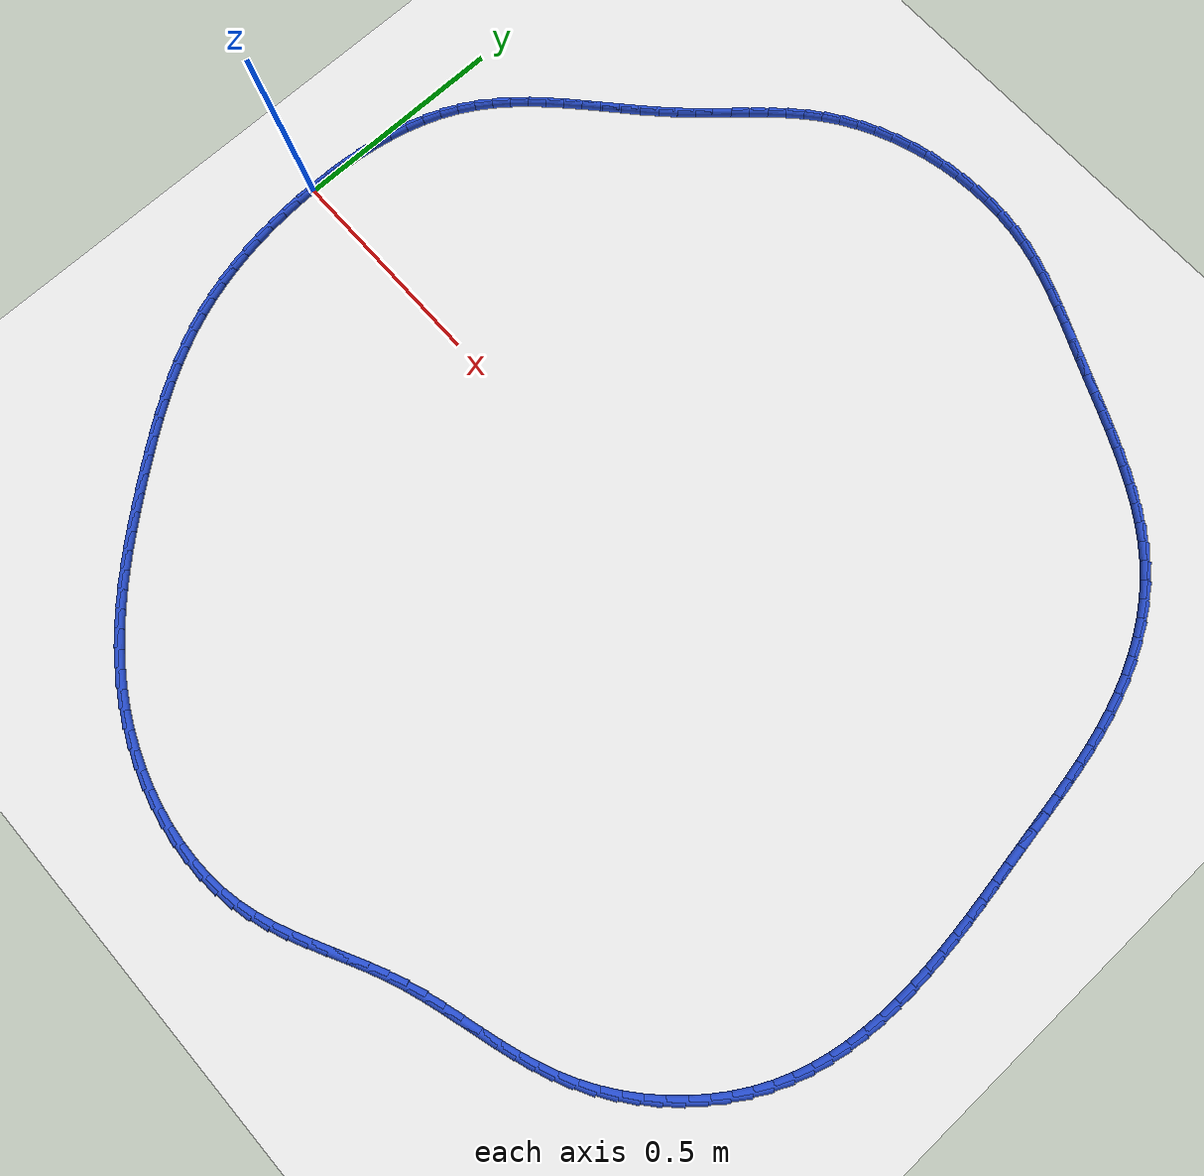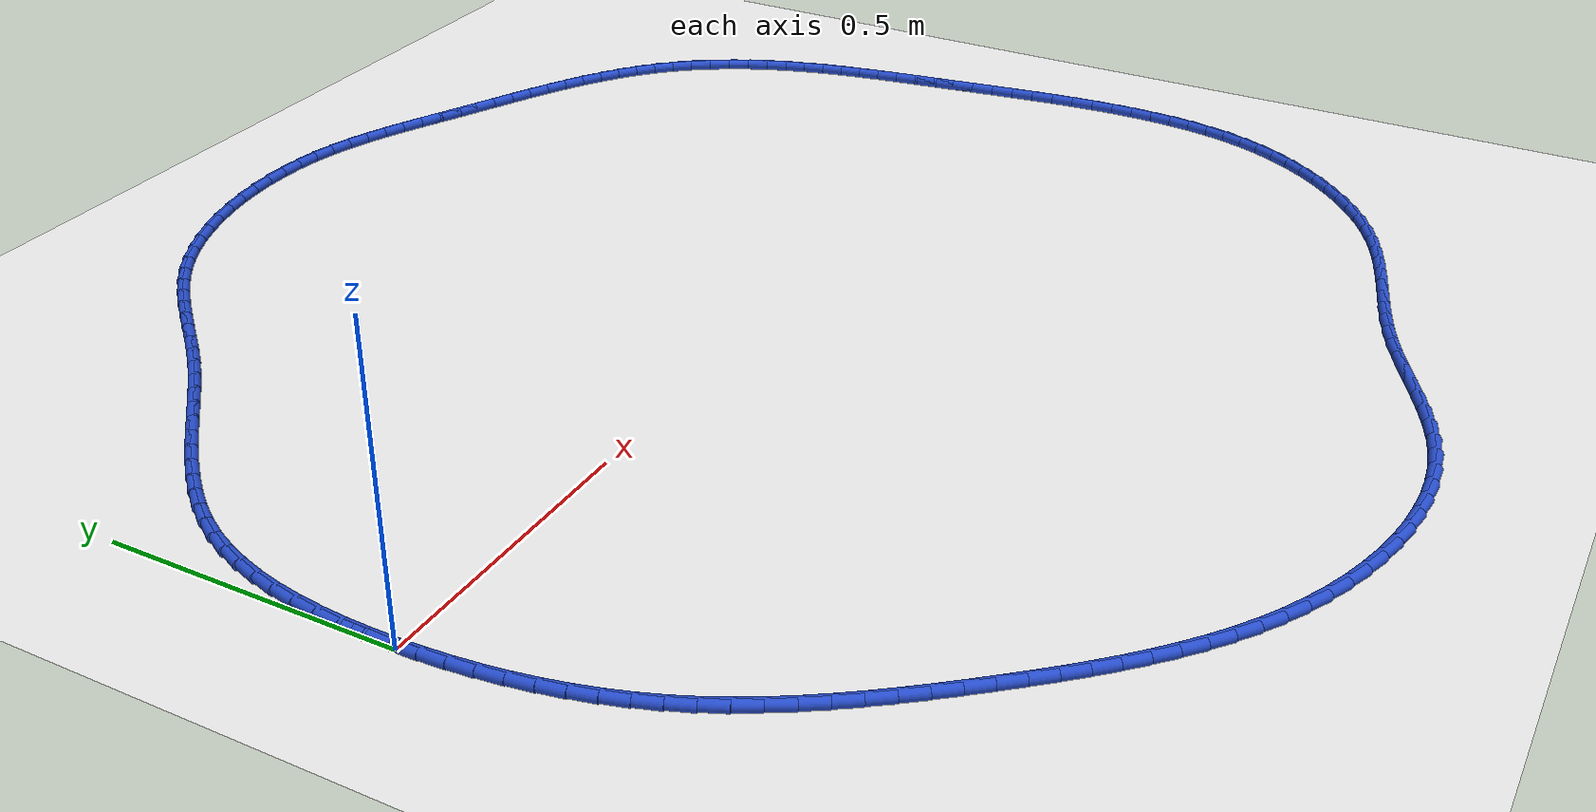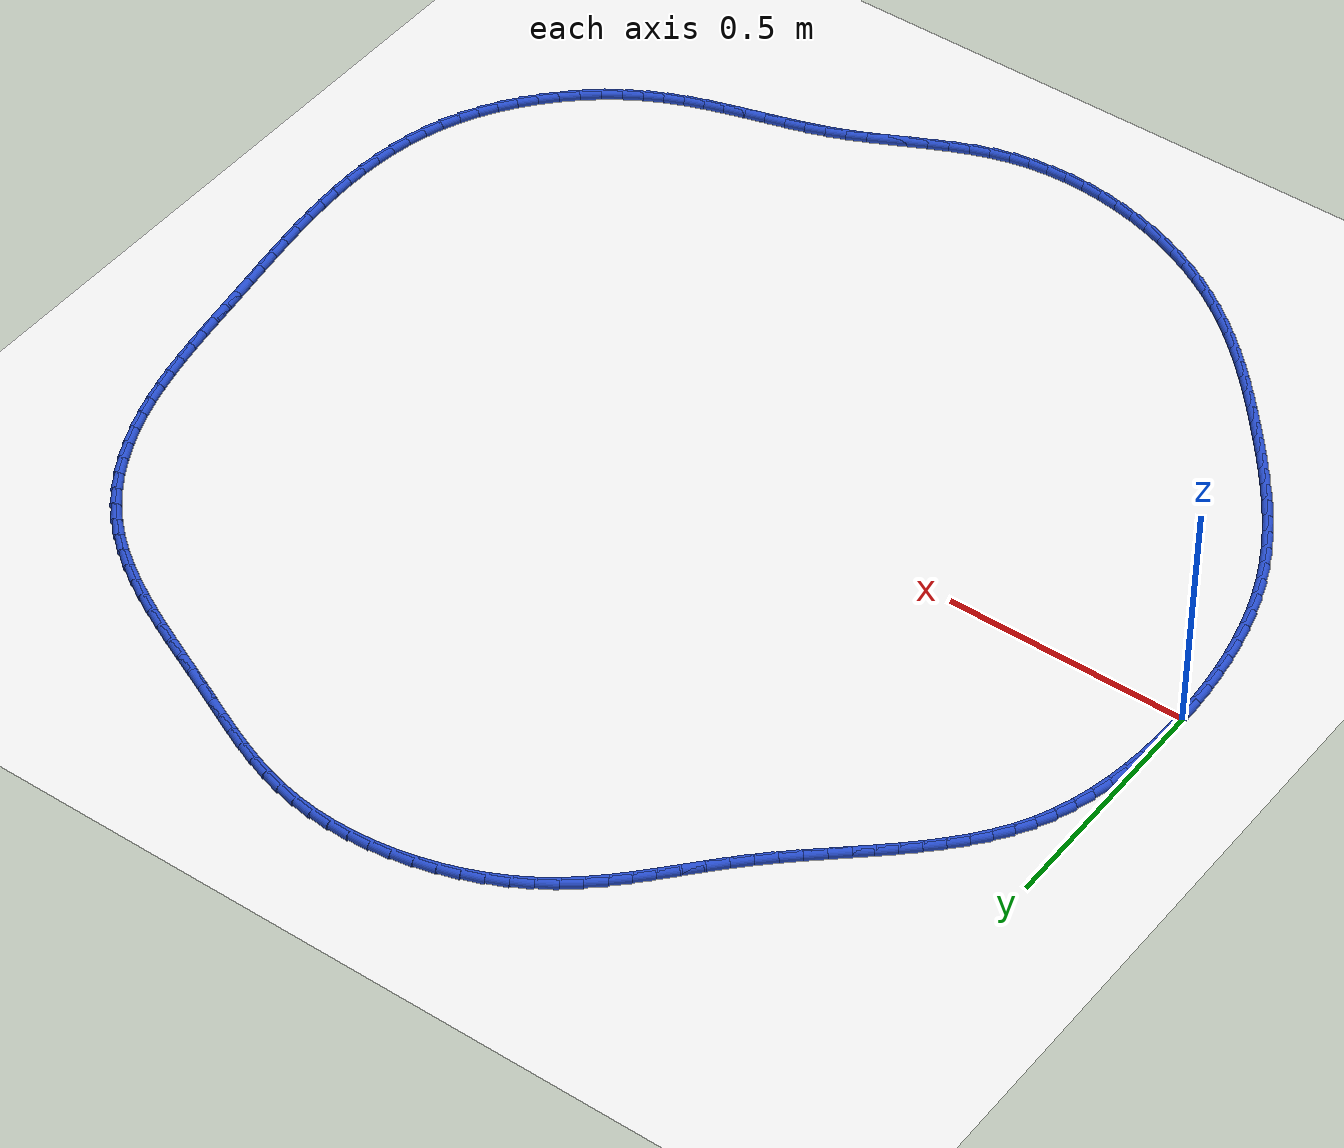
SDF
<sdf version="1.6">
 <world name="default">
  <light name="sun" type="directional">
   <pose>0 0 10 0 -0 0</pose>
   <diffuse>0.8 0.8 0.8 1</diffuse>
   <specular>0.2 0.2 0.2 1</specular>
   <attenuation>
    <range>1000</range>
    <constant>0.9</constant>
    <linear>0.01</linear>
    <quadratic>0.001</quadratic>
   </attenuation>
   <direction>-0.5 0.1 -0.9</direction>
  </light>
  <model name="ground_plane">
   <static>1</static>
   <link name="link">
    <collision name="collision">
     <geometry><plane><normal>0 0 1</normal><size>100 100</size></plane></geometry>
     <surface><friction><ode><mu>100</mu><mu2>50</mu2></ode></friction></surface>
    </collision>
    <visual name="visual">
     <cast_shadows>0</cast_shadows>
     <geometry><plane><normal>0 0 1</normal><size>100 100</size></plane></geometry>
     <material>
      <script><uri>file://media/materials/scripts/gazebo.material</uri><name>Gazebo/WhiteGlow</name></script>
     </material>
    </visual>
   </link>
  </model>
  <gravity>0 0 -9.8</gravity>
  <magnetic_field>6e-06 2.3e-05 -4.2e-05</magnetic_field>
  <atmosphere type="adiabatic"/>
  <physics name="default_physics" default="0" type="ode">
   <max_step_size>0.001</max_step_size>
   <real_time_factor>1</real_time_factor>
   <real_time_update_rate>1000</real_time_update_rate>
  </physics>
  <scene><ambient>0.4 0.4 0.4 1</ambient><background>0.7 0.7 0.7 1</background><shadows>1</shadows></scene>
  <spherical_coordinates>
   <surface_model>EARTH_WGS84</surface_model>
   <latitude_deg>0</latitude_deg>
   <longitude_deg>0</longitude_deg>
   <elevation>0</elevation>
   <heading_deg>0</heading_deg>
  </spherical_coordinates>
  <model name="line">
   <link name="link_0">
    <pose>-1.6479873021779667e-17 -8.326672684688674e-17 0.01 0 1.57 -1.5696141677985251</pose>
    <collision name="collision">
     <geometry><cylinder><radius>0.01</radius><length>0.08</length></cylinder></geometry>
    </collision>
    <visual name="visual">
     <material>
      <script><name>Gazebo/Blue</name><uri>file://media/materials/scripts/gazebo.material</uri></script>
     </material>
     <geometry><cylinder><radius>0.01</radius><length>0.08</length></cylinder></geometry>
    </visual>
   </link>
   <link name="link_1">
    <pose>-5.092528736734469e-05 0.04307818474582921 0.01 0 1.57 1.536348133848838</pose>
    <collision name="collision">
     <geometry><cylinder><radius>0.01</radius><length>0.08</length></cylinder></geometry>
    </collision>
    <visual name="visual">
     <material>
      <script><name>Gazebo/Blue</name><uri>file://media/materials/scripts/gazebo.material</uri></script>
     </material>
     <geometry><cylinder><radius>0.01</radius><length>0.08</length></cylinder></geometry>
    </visual>
   </link>
   <link name="link_2">
    <pose>0.0014344221991047141 0.08617942663825474 0.01 0 1.57 1.4964940591130282</pose>
    <collision name="collision">
     <geometry><cylinder><radius>0.01</radius><length>0.08</length></cylinder></geometry>
    </collision>
    <visual name="visual">
     <material>
      <script><name>Gazebo/Blue</name><uri>file://media/materials/scripts/gazebo.material</uri></script>
     </material>
     <geometry><cylinder><radius>0.01</radius><length>0.08</length></cylinder></geometry>
    </visual>
   </link>
   <link name="link_3">
    <pose>0.004627960893907758 0.12908066826286146 0.01 0 1.57 1.4519182333033531</pose>
    <collision name="collision">
     <geometry><cylinder><radius>0.01</radius><length>0.08</length></cylinder></geometry>
    </collision>
    <visual name="visual">
     <material>
      <script><name>Gazebo/Blue</name><uri>file://media/materials/scripts/gazebo.material</uri></script>
     </material>
     <geometry><cylinder><radius>0.01</radius><length>0.08</length></cylinder></geometry>
    </visual>
   </link>
   <link name="link_4">
    <pose>0.009701609231533365 0.1715588522052341 0.01 0 1.57 1.4020756962306076</pose>
    <collision name="collision">
     <geometry><cylinder><radius>0.01</radius><length>0.08</length></cylinder></geometry>
    </collision>
    <visual name="visual">
     <material>
      <script><name>Gazebo/Blue</name><uri>file://media/materials/scripts/gazebo.material</uri></script>
     </material>
     <geometry><cylinder><radius>0.01</radius><length>0.08</length></cylinder></geometry>
    </visual>
   </link>
   <link name="link_5">
    <pose>0.016827285646473136 0.2133909210509577 0.01 0 1.57 1.3463943189602026</pose>
    <collision name="collision">
     <geometry><cylinder><radius>0.01</radius><length>0.08</length></cylinder></geometry>
    </collision>
    <visual name="visual">
     <material>
      <script><name>Gazebo/Blue</name><uri>file://media/materials/scripts/gazebo.material</uri></script>
     </material>
     <geometry><cylinder><radius>0.01</radius><length>0.08</length></cylinder></geometry>
    </visual>
   </link>
   <link name="link_6">
    <pose>0.026176908573218673 0.2543538173856171 0.01 0 1.57 1.284310466505673</pose>
    <collision name="collision">
     <geometry><cylinder><radius>0.01</radius><length>0.08</length></cylinder></geometry>
    </collision>
    <visual name="visual">
     <material>
      <script><name>Gazebo/Blue</name><uri>file://media/materials/scripts/gazebo.material</uri></script>
     </material>
     <geometry><cylinder><radius>0.01</radius><length>0.08</length></cylinder></geometry>
    </visual>
   </link>
   <link name="link_7">
    <pose>0.037922396446261525 0.294224483794797 0.01 0 1.57 1.2153267936622847</pose>
    <collision name="collision">
     <geometry><cylinder><radius>0.01</radius><length>0.08</length></cylinder></geometry>
    </collision>
    <visual name="visual">
     <material>
      <script><name>Gazebo/Blue</name><uri>file://media/materials/scripts/gazebo.material</uri></script>
     </material>
     <geometry><cylinder><radius>0.01</radius><length>0.08</length></cylinder></geometry>
    </visual>
   </link>
   <link name="link_8">
    <pose>0.0522356677000933 0.33277986286408223 0.01 0 1.57 1.1390972540197581</pose>
    <collision name="collision">
     <geometry><cylinder><radius>0.01</radius><length>0.08</length></cylinder></geometry>
    </collision>
    <visual name="visual">
     <material>
      <script><name>Gazebo/Blue</name><uri>file://media/materials/scripts/gazebo.material</uri></script>
     </material>
     <geometry><cylinder><radius>0.01</radius><length>0.08</length></cylinder></geometry>
    </visual>
   </link>
   <link name="link_9">
    <pose>0.06928864076920561 0.369796897179058 0.01 0 1.57 1.0562807380471253</pose>
    <collision name="collision">
     <geometry><cylinder><radius>0.01</radius><length>0.08</length></cylinder></geometry>
    </collision>
    <visual name="visual">
     <material>
      <script><name>Gazebo/Blue</name><uri>file://media/materials/scripts/gazebo.material</uri></script>
     </material>
     <geometry><cylinder><radius>0.01</radius><length>0.08</length></cylinder></geometry>
    </visual>
   </link>
   <link name="link_10">
    <pose>0.08923008699137204 0.405072624164393 0.01 0 1.57 0.9768405126058521</pose>
    <collision name="collision">
     <geometry><cylinder><radius>0.01</radius><length>0.08</length></cylinder></geometry>
    </collision>
    <visual name="visual">
     <material>
      <script><name>Gazebo/Blue</name><uri>file://media/materials/scripts/gazebo.material</uri></script>
     </material>
     <geometry><cylinder><radius>0.01</radius><length>0.08</length></cylinder></geometry>
    </visual>
   </link>
   <link name="link_11">
    <pose>0.11191251096359234 0.4386612812104513 0.01 0 1.57 0.9082398506536468</pose>
    <collision name="collision">
     <geometry><cylinder><radius>0.01</radius><length>0.08</length></cylinder></geometry>
    </collision>
    <visual name="visual">
     <material>
      <script><name>Gazebo/Blue</name><uri>file://media/materials/scripts/gazebo.material</uri></script>
     </material>
     <geometry><cylinder><radius>0.01</radius><length>0.08</length></cylinder></geometry>
    </visual>
   </link>
   <link name="link_12">
    <pose>0.13698352509505812 0.47079498009045223 0.01 0 1.57 0.8509957041564209</pose>
    <collision name="collision">
     <geometry><cylinder><radius>0.01</radius><length>0.08</length></cylinder></geometry>
    </collision>
    <visual name="visual">
     <material>
      <script><name>Gazebo/Blue</name><uri>file://media/materials/scripts/gazebo.material</uri></script>
     </material>
     <geometry><cylinder><radius>0.01</radius><length>0.08</length></cylinder></geometry>
    </visual>
   </link>
   <link name="link_13">
    <pose>0.16408665229023406 0.501709382825856 0.01 0 1.57 0.8050177651373709</pose>
    <collision name="collision">
     <geometry><cylinder><radius>0.01</radius><length>0.08</length></cylinder></geometry>
    </collision>
    <visual name="visual">
     <material>
      <script><name>Gazebo/Blue</name><uri>file://media/materials/scripts/gazebo.material</uri></script>
     </material>
     <geometry><cylinder><radius>0.01</radius><length>0.08</length></cylinder></geometry>
    </visual>
   </link>
   <link name="link_14">
    <pose>0.192865415453585 0.5316401514381229 0.01 0 1.57 0.7699622364212031</pose>
    <collision name="collision">
     <geometry><cylinder><radius>0.01</radius><length>0.08</length></cylinder></geometry>
    </collision>
    <visual name="visual">
     <material>
      <script><name>Gazebo/Blue</name><uri>file://media/materials/scripts/gazebo.material</uri></script>
     </material>
     <geometry><cylinder><radius>0.01</radius><length>0.08</length></cylinder></geometry>
    </visual>
   </link>
   <link name="link_15">
    <pose>0.22296333748957556 0.5608229479487133 0.01 0 1.57 0.7454048712055941</pose>
    <collision name="collision">
     <geometry><cylinder><radius>0.01</radius><length>0.08</length></cylinder></geometry>
    </collision>
    <visual name="visual">
     <material>
      <script><name>Gazebo/Blue</name><uri>file://media/materials/scripts/gazebo.material</uri></script>
     </material>
     <geometry><cylinder><radius>0.01</radius><length>0.08</length></cylinder></geometry>
    </visual>
   </link>
   <link name="link_16">
    <pose>0.2540239413026707 0.5894934343790881 0.01 0 1.57 0.7309575903352178</pose>
    <collision name="collision">
     <geometry><cylinder><radius>0.01</radius><length>0.08</length></cylinder></geometry>
    </collision>
    <visual name="visual">
     <material>
      <script><name>Gazebo/Blue</name><uri>file://media/materials/scripts/gazebo.material</uri></script>
     </material>
     <geometry><cylinder><radius>0.01</radius><length>0.08</length></cylinder></geometry>
    </visual>
   </link>
   <link name="link_17">
    <pose>0.285690749797335 0.6178872727507071 0.01 0 1.57 0.726337679582761</pose>
    <collision name="collision">
     <geometry><cylinder><radius>0.01</radius><length>0.08</length></cylinder></geometry>
    </collision>
    <visual name="visual">
     <material>
      <script><name>Gazebo/Blue</name><uri>file://media/materials/scripts/gazebo.material</uri></script>
     </material>
     <geometry><cylinder><radius>0.01</radius><length>0.08</length></cylinder></geometry>
    </visual>
   </link>
   <link name="link_18">
    <pose>0.3176072858780333 0.646240125085031 0.01 0 1.57 0.7314016075255899</pose>
    <collision name="collision">
     <geometry><cylinder><radius>0.01</radius><length>0.08</length></cylinder></geometry>
    </collision>
    <visual name="visual">
     <material>
      <script><name>Gazebo/Blue</name><uri>file://media/materials/scripts/gazebo.material</uri></script>
     </material>
     <geometry><cylinder><radius>0.01</radius><length>0.08</length></cylinder></geometry>
    </visual>
   </link>
   <link name="link_19">
    <pose>0.3494170724492303 0.6747876534035203 0.01 0 1.57 0.7461524125041278</pose>
    <collision name="collision">
     <geometry><cylinder><radius>0.01</radius><length>0.08</length></cylinder></geometry>
    </collision>
    <visual name="visual">
     <material>
      <script><name>Gazebo/Blue</name><uri>file://media/materials/scripts/gazebo.material</uri></script>
     </material>
     <geometry><cylinder><radius>0.01</radius><length>0.08</length></cylinder></geometry>
    </visual>
   </link>
   <link name="link_20">
    <pose>0.38076363241539085 0.7037655197276352 0.01 0 1.57 0.7707244732574585</pose>
    <collision name="collision">
     <geometry><cylinder><radius>0.01</radius><length>0.08</length></cylinder></geometry>
    </collision>
    <visual name="visual">
     <material>
      <script><name>Gazebo/Blue</name><uri>file://media/materials/scripts/gazebo.material</uri></script>
     </material>
     <geometry><cylinder><radius>0.01</radius><length>0.08</length></cylinder></geometry>
    </visual>
   </link>
   <link name="link_21">
    <pose>0.4112904886809796 0.7334093860788361 0.01 0 1.57 0.8033352467335615</pose>
    <collision name="collision">
     <geometry><cylinder><radius>0.01</radius><length>0.08</length></cylinder></geometry>
    </collision>
    <visual name="visual">
     <material>
      <script><name>Gazebo/Blue</name><uri>file://media/materials/scripts/gazebo.material</uri></script>
     </material>
     <geometry><cylinder><radius>0.01</radius><length>0.08</length></cylinder></geometry>
    </visual>
   </link>
   <link name="link_22">
    <pose>0.4407071087868779 0.7639006949583271 0.01 0 1.57 0.8291740088223976</pose>
    <collision name="collision">
     <geometry><cylinder><radius>0.01</radius><length>0.08</length></cylinder></geometry>
    </collision>
    <visual name="visual">
     <material>
      <script><name>Gazebo/Blue</name><uri>file://media/materials/scripts/gazebo.material</uri></script>
     </material>
     <geometry><cylinder><radius>0.01</radius><length>0.08</length></cylinder></geometry>
    </visual>
   </link>
   <link name="link_23">
    <pose>0.4692128195523241 0.795018127755733 0.01 0 1.57 0.8413790691090767</pose>
    <collision name="collision">
     <geometry><cylinder><radius>0.01</radius><length>0.08</length></cylinder></geometry>
    </collision>
    <visual name="visual">
     <material>
      <script><name>Gazebo/Blue</name><uri>file://media/materials/scripts/gazebo.material</uri></script>
     </material>
     <geometry><cylinder><radius>0.01</radius><length>0.08</length></cylinder></geometry>
    </visual>
   </link>
   <link name="link_24">
    <pose>0.4972274812149523 0.8263590438184976 0.01 0 1.57 0.8397617513056158</pose>
    <collision name="collision">
     <geometry><cylinder><radius>0.01</radius><length>0.08</length></cylinder></geometry>
    </collision>
    <visual name="visual">
     <material>
      <script><name>Gazebo/Blue</name><uri>file://media/materials/scripts/gazebo.material</uri></script>
     </material>
     <geometry><cylinder><radius>0.01</radius><length>0.08</length></cylinder></geometry>
    </visual>
   </link>
   <link name="link_25">
    <pose>0.525172015375039 0.8575199298442716 0.01 0 1.57 0.8241406312690777</pose>
    <collision name="collision">
     <geometry><cylinder><radius>0.01</radius><length>0.08</length></cylinder></geometry>
    </collision>
    <visual name="visual">
     <material>
      <script><name>Gazebo/Blue</name><uri>file://media/materials/scripts/gazebo.material</uri></script>
     </material>
     <geometry><cylinder><radius>0.01</radius><length>0.08</length></cylinder></geometry>
    </visual>
   </link>
   <link name="link_26">
    <pose>0.5534673436328607 0.8880972725307065 0.01 0 1.57 0.7943182456971727</pose>
    <collision name="collision">
     <geometry><cylinder><radius>0.01</radius><length>0.08</length></cylinder></geometry>
    </collision>
    <visual name="visual">
     <material>
      <script><name>Gazebo/Blue</name><uri>file://media/materials/scripts/gazebo.material</uri></script>
     </material>
     <geometry><cylinder><radius>0.01</radius><length>0.08</length></cylinder></geometry>
    </visual>
   </link>
   <link name="link_27">
    <pose>0.582534387588694 0.9176875585754533 0.01 0 1.57 0.7501752005780918</pose>
    <collision name="collision">
     <geometry><cylinder><radius>0.01</radius><length>0.08</length></cylinder></geometry>
    </collision>
    <visual name="visual">
     <material>
      <script><name>Gazebo/Blue</name><uri>file://media/materials/scripts/gazebo.material</uri></script>
     </material>
     <geometry><cylinder><radius>0.01</radius><length>0.08</length></cylinder></geometry>
    </visual>
   </link>
   <link name="link_28">
    <pose>0.6127940688428153 0.9458872746761625 0.01 0 1.57 0.6918539752741508</pose>
    <collision name="collision">
     <geometry><cylinder><radius>0.01</radius><length>0.08</length></cylinder></geometry>
    </collision>
    <visual name="visual">
     <material>
      <script><name>Gazebo/Blue</name><uri>file://media/materials/scripts/gazebo.material</uri></script>
     </material>
     <geometry><cylinder><radius>0.01</radius><length>0.08</length></cylinder></geometry>
    </visual>
   </link>
   <link name="link_29">
    <pose>0.644667308995501 0.9722929075304855 0.01 0 1.57 0.6203816824784673</pose>
    <collision name="collision">
     <geometry><cylinder><radius>0.01</radius><length>0.08</length></cylinder></geometry>
    </collision>
    <visual name="visual">
     <material>
      <script><name>Gazebo/Blue</name><uri>file://media/materials/scripts/gazebo.material</uri></script>
     </material>
     <geometry><cylinder><radius>0.01</radius><length>0.08</length></cylinder></geometry>
    </visual>
   </link>
   <link name="link_30">
    <pose>0.6785599540155693 0.9965087067793307 0.01 0 1.57 0.5447760766698809</pose>
    <collision name="collision">
     <geometry><cylinder><radius>0.01</radius><length>0.08</length></cylinder></geometry>
    </collision>
    <visual name="visual">
     <material>
      <script><name>Gazebo/Blue</name><uri>file://media/materials/scripts/gazebo.material</uri></script>
     </material>
     <geometry><cylinder><radius>0.01</radius><length>0.08</length></cylinder></geometry>
    </visual>
   </link>
   <link name="link_31">
    <pose>0.7145421572466443 1.0183117813437406 0.01 0 1.57 0.4727266441883336</pose>
    <collision name="collision">
     <geometry><cylinder><radius>0.01</radius><length>0.08</length></cylinder></geometry>
    </collision>
    <visual name="visual">
     <material>
      <script><name>Gazebo/Blue</name><uri>file://media/materials/scripts/gazebo.material</uri></script>
     </material>
     <geometry><cylinder><radius>0.01</radius><length>0.08</length></cylinder></geometry>
    </visual>
   </link>
   <link name="link_32">
    <pose>0.7523544042412301 1.037648997037755 0.01 0 1.57 0.4038822681004972</pose>
    <collision name="collision">
     <geometry><cylinder><radius>0.01</radius><length>0.08</length></cylinder></geometry>
    </collision>
    <visual name="visual">
     <material>
      <script><name>Gazebo/Blue</name><uri>file://media/materials/scripts/gazebo.material</uri></script>
     </material>
     <geometry><cylinder><radius>0.01</radius><length>0.08</length></cylinder></geometry>
    </visual>
   </link>
   <link name="link_33">
    <pose>0.7917233100110839 1.054474362077449 0.01 0 1.57 0.33753491464490193</pose>
    <collision name="collision">
     <geometry><cylinder><radius>0.01</radius><length>0.08</length></cylinder></geometry>
    </collision>
    <visual name="visual">
     <material>
      <script><name>Gazebo/Blue</name><uri>file://media/materials/scripts/gazebo.material</uri></script>
     </material>
     <geometry><cylinder><radius>0.01</radius><length>0.08</length></cylinder></geometry>
    </visual>
   </link>
   <link name="link_34">
    <pose>0.8323754895679619 1.068741884678896 0.01 0 1.57 0.27297107034029305</pose>
    <collision name="collision">
     <geometry><cylinder><radius>0.01</radius><length>0.08</length></cylinder></geometry>
    </collision>
    <visual name="visual">
     <material>
      <script><name>Gazebo/Blue</name><uri>file://media/materials/scripts/gazebo.material</uri></script>
     </material>
     <geometry><cylinder><radius>0.01</radius><length>0.08</length></cylinder></geometry>
    </visual>
   </link>
   <link name="link_35">
    <pose>0.8740375579236208 1.0804055730581705 0.01 0 1.57 0.2094793990500455</pose>
    <collision name="collision">
     <geometry><cylinder><radius>0.01</radius><length>0.08</length></cylinder></geometry>
    </collision>
    <visual name="visual">
     <material>
      <script><name>Gazebo/Blue</name><uri>file://media/materials/scripts/gazebo.material</uri></script>
     </material>
     <geometry><cylinder><radius>0.01</radius><length>0.08</length></cylinder></geometry>
    </visual>
   </link>
   <link name="link_36">
    <pose>0.9164361300898182 1.089419435431347 0.01 0 1.57 0.14635147796256123</pose>
    <collision name="collision">
     <geometry><cylinder><radius>0.01</radius><length>0.08</length></cylinder></geometry>
    </collision>
    <visual name="visual">
     <material>
      <script><name>Gazebo/Blue</name><uri>file://media/materials/scripts/gazebo.material</uri></script>
     </material>
     <geometry><cylinder><radius>0.01</radius><length>0.08</length></cylinder></geometry>
    </visual>
   </link>
   <link name="link_37">
    <pose>0.9592978210783093 1.0957374800144988 0.01 0 1.57 0.0828786281595138</pose>
    <collision name="collision">
     <geometry><cylinder><radius>0.01</radius><length>0.08</length></cylinder></geometry>
    </collision>
    <visual name="visual">
     <material>
      <script><name>Gazebo/Blue</name><uri>file://media/materials/scripts/gazebo.material</uri></script>
     </material>
     <geometry><cylinder><radius>0.01</radius><length>0.08</length></cylinder></geometry>
    </visual>
   </link>
   <link name="link_38">
    <pose>1.0023492459008523 1.099313715023701 0.01 0 1.57 0.018347359266134493</pose>
    <collision name="collision">
     <geometry><cylinder><radius>0.01</radius><length>0.08</length></cylinder></geometry>
    </collision>
    <visual name="visual">
     <material>
      <script><name>Gazebo/Blue</name><uri>file://media/materials/scripts/gazebo.material</uri></script>
     </material>
     <geometry><cylinder><radius>0.01</radius><length>0.08</length></cylinder></geometry>
    </visual>
   </link>
   <link name="link_39">
    <pose>1.0453170195692028 1.100102148675027 0.01 0 1.57 -0.04796421919625381</pose>
    <collision name="collision">
     <geometry><cylinder><radius>0.01</radius><length>0.08</length></cylinder></geometry>
    </collision>
    <visual name="visual">
     <material>
      <script><name>Gazebo/Blue</name><uri>file://media/materials/scripts/gazebo.material</uri></script>
     </material>
     <geometry><cylinder><radius>0.01</radius><length>0.08</length></cylinder></geometry>
    </visual>
   </link>
   <link name="link_40">
    <pose>1.0879277570951178 1.0980567891845514 0.01 0 1.57 -0.11678646031318861</pose>
    <collision name="collision">
     <geometry><cylinder><radius>0.01</radius><length>0.08</length></cylinder></geometry>
    </collision>
    <visual name="visual">
     <material>
      <script><name>Gazebo/Blue</name><uri>file://media/materials/scripts/gazebo.material</uri></script>
     </material>
     <geometry><cylinder><radius>0.01</radius><length>0.08</length></cylinder></geometry>
    </visual>
   </link>
   <link name="link_41">
    <pose>1.129908073490354 1.093131644768348 0.01 0 1.57 -0.18860787591641537</pose>
    <collision name="collision">
     <geometry><cylinder><radius>0.01</radius><length>0.08</length></cylinder></geometry>
    </collision>
    <visual name="visual">
     <material>
      <script><name>Gazebo/Blue</name><uri>file://media/materials/scripts/gazebo.material</uri></script>
     </material>
     <geometry><cylinder><radius>0.01</radius><length>0.08</length></cylinder></geometry>
    </visual>
   </link>
   <link name="link_42">
    <pose>1.1709930747108805 1.0852894790727863 0.01 0 1.57 -0.257580707574147</pose>
    <collision name="collision">
     <geometry><cylinder><radius>0.01</radius><length>0.08</length></cylinder></geometry>
    </collision>
    <visual name="visual">
     <material>
      <script><name>Gazebo/Blue</name><uri>file://media/materials/scripts/gazebo.material</uri></script>
     </material>
     <geometry><cylinder><radius>0.01</radius><length>0.08</length></cylinder></geometry>
    </visual>
   </link>
   <link name="link_43">
    <pose>1.211133324264604 1.0747152246256129 0.01 0 1.57 -0.3163138986401706</pose>
    <collision name="collision">
     <geometry><cylinder><radius>0.01</radius><length>0.08</length></cylinder></geometry>
    </collision>
    <visual name="visual">
     <material>
      <script><name>Gazebo/Blue</name><uri>file://media/materials/scripts/gazebo.material</uri></script>
     </material>
     <geometry><cylinder><radius>0.01</radius><length>0.08</length></cylinder></geometry>
    </visual>
   </link>
   <link name="link_44">
    <pose>1.2505066801687879 1.0618281885050718 0.01 0 1.57 -0.36375824159920217</pose>
    <collision name="collision">
     <geometry><cylinder><radius>0.01</radius><length>0.08</length></cylinder></geometry>
    </collision>
    <visual name="visual">
     <material>
      <script><name>Gazebo/Blue</name><uri>file://media/materials/scripts/gazebo.material</uri></script>
     </material>
     <geometry><cylinder><radius>0.01</radius><length>0.08</length></cylinder></geometry>
    </visual>
   </link>
   <link name="link_45">
    <pose>1.2893018608993845 1.0470588765426507 0.01 0 1.57 -0.3996333123550256</pose>
    <collision name="collision">
     <geometry><cylinder><radius>0.01</radius><length>0.08</length></cylinder></geometry>
    </collision>
    <visual name="visual">
     <material>
      <script><name>Gazebo/Blue</name><uri>file://media/materials/scripts/gazebo.material</uri></script>
     </material>
     <geometry><cylinder><radius>0.01</radius><length>0.08</length></cylinder></geometry>
    </visual>
   </link>
   <link name="link_46">
    <pose>1.327707584932346 1.030837794569836 0.01 0 1.57 -0.4239439633681479</pose>
    <collision name="collision">
     <geometry><cylinder><radius>0.01</radius><length>0.08</length></cylinder></geometry>
    </collision>
    <visual name="visual">
     <material>
      <script><name>Gazebo/Blue</name><uri>file://media/materials/scripts/gazebo.material</uri></script>
     </material>
     <geometry><cylinder><radius>0.01</radius><length>0.08</length></cylinder></geometry>
    </visual>
   </link>
   <link name="link_47">
    <pose>1.365912570743625 1.0135954484181144 0.01 0 1.57 -0.43683613150107903</pose>
    <collision name="collision">
     <geometry><cylinder><radius>0.01</radius><length>0.08</length></cylinder></geometry>
    </collision>
    <visual name="visual">
     <material>
      <script><name>Gazebo/Blue</name><uri>file://media/materials/scripts/gazebo.material</uri></script>
     </material>
     <geometry><cylinder><radius>0.01</radius><length>0.08</length></cylinder></geometry>
    </visual>
   </link>
   <link name="link_48">
    <pose>1.4041055368091742 0.9957623439189733 0.01 0 1.57 -0.4384984399056323</pose>
    <collision name="collision">
     <geometry><cylinder><radius>0.01</radius><length>0.08</length></cylinder></geometry>
    </collision>
    <visual name="visual">
     <material>
      <script><name>Gazebo/Blue</name><uri>file://media/materials/scripts/gazebo.material</uri></script>
     </material>
     <geometry><cylinder><radius>0.01</radius><length>0.08</length></cylinder></geometry>
    </visual>
   </link>
   <link name="link_49">
    <pose>1.4424752016049454 0.9777689869038989 0.01 0 1.57 -0.4313074848804435</pose>
    <collision name="collision">
     <geometry><cylinder><radius>0.01</radius><length>0.08</length></cylinder></geometry>
    </collision>
    <visual name="visual">
     <material>
      <script><name>Gazebo/Blue</name><uri>file://media/materials/scripts/gazebo.material</uri></script>
     </material>
     <geometry><cylinder><radius>0.01</radius><length>0.08</length></cylinder></geometry>
    </visual>
   </link>
   <link name="link_50">
    <pose>1.4811609476985994 0.9599656337694764 0.01 0 1.57 -0.4273607068896546</pose>
    <collision name="collision">
     <geometry><cylinder><radius>0.01</radius><length>0.08</length></cylinder></geometry>
    </collision>
    <visual name="visual">
     <material>
      <script><name>Gazebo/Blue</name><uri>file://media/materials/scripts/gazebo.material</uri></script>
     </material>
     <geometry><cylinder><radius>0.01</radius><length>0.08</length></cylinder></geometry>
    </visual>
   </link>
   <link name="link_51">
    <pose>1.520031744659747 0.9422626890673529 0.01 0 1.57 -0.43069311473965033</pose>
    <collision name="collision">
     <geometry><cylinder><radius>0.01</radius><length>0.08</length></cylinder></geometry>
    </collision>
    <visual name="visual">
     <material>
      <script><name>Gazebo/Blue</name><uri>file://media/materials/scripts/gazebo.material</uri></script>
     </material>
     <geometry><cylinder><radius>0.01</radius><length>0.08</length></cylinder></geometry>
    </visual>
   </link>
   <link name="link_52">
    <pose>1.558864391684482 0.9244206336800799 0.01 0 1.57 -0.44131992798824843</pose>
    <collision name="collision">
     <geometry><cylinder><radius>0.01</radius><length>0.08</length></cylinder></geometry>
    </collision>
    <visual name="visual">
     <material>
      <script><name>Gazebo/Blue</name><uri>file://media/materials/scripts/gazebo.material</uri></script>
     </material>
     <geometry><cylinder><radius>0.01</radius><length>0.08</length></cylinder></geometry>
    </visual>
   </link>
   <link name="link_53">
    <pose>1.5974356099540368 0.90619982159179 0.01 0 1.57 -0.45935259824972974</pose>
    <collision name="collision">
     <geometry><cylinder><radius>0.01</radius><length>0.08</length></cylinder></geometry>
    </collision>
    <visual name="visual">
     <material>
      <script><name>Gazebo/Blue</name><uri>file://media/materials/scripts/gazebo.material</uri></script>
     </material>
     <geometry><cylinder><radius>0.01</radius><length>0.08</length></cylinder></geometry>
    </visual>
   </link>
   <link name="link_54">
    <pose>1.6355221206496413 0.8873606067866162 0.01 0 1.57 -0.484988050522203</pose>
    <collision name="collision">
     <geometry><cylinder><radius>0.01</radius><length>0.08</length></cylinder></geometry>
    </collision>
    <visual name="visual">
     <material>
      <script><name>Gazebo/Blue</name><uri>file://media/materials/scripts/gazebo.material</uri></script>
     </material>
     <geometry><cylinder><radius>0.01</radius><length>0.08</length></cylinder></geometry>
    </visual>
   </link>
   <link name="link_55">
    <pose>1.6729006449525263 0.8676633432486908 0.01 0 1.57 -0.5184830303943455</pose>
    <collision name="collision">
     <geometry><cylinder><radius>0.01</radius><length>0.08</length></cylinder></geometry>
    </collision>
    <visual name="visual">
     <material>
      <script><name>Gazebo/Blue</name><uri>file://media/materials/scripts/gazebo.material</uri></script>
     </material>
     <geometry><cylinder><radius>0.01</radius><length>0.08</length></cylinder></geometry>
    </visual>
   </link>
   <link name="link_56">
    <pose>1.7093479040439243 0.8468683849621463 0.01 0 1.57 -0.5601128313264404</pose>
    <collision name="collision">
     <geometry><cylinder><radius>0.01</radius><length>0.08</length></cylinder></geometry>
    </collision>
    <visual name="visual">
     <material>
      <script><name>Gazebo/Blue</name><uri>file://media/materials/scripts/gazebo.material</uri></script>
     </material>
     <geometry><cylinder><radius>0.01</radius><length>0.08</length></cylinder></geometry>
    </visual>
   </link>
   <link name="link_57">
    <pose>1.7446406191050652 0.8247360859111158 0.01 0 1.57 -0.6101094952772512</pose>
    <collision name="collision">
     <geometry><cylinder><radius>0.01</radius><length>0.08</length></cylinder></geometry>
    </collision>
    <visual name="visual">
     <material>
      <script><name>Gazebo/Blue</name><uri>file://media/materials/scripts/gazebo.material</uri></script>
     </material>
     <geometry><cylinder><radius>0.01</radius><length>0.08</length></cylinder></geometry>
    </visual>
   </link>
   <link name="link_58">
    <pose>1.77855551131718 0.8010268000797313 0.01 0 1.57 -0.6685759168220262</pose>
    <collision name="collision">
     <geometry><cylinder><radius>0.01</radius><length>0.08</length></cylinder></geometry>
    </collision>
    <visual name="visual">
     <material>
      <script><name>Gazebo/Blue</name><uri>file://media/materials/scripts/gazebo.material</uri></script>
     </material>
     <geometry><cylinder><radius>0.01</radius><length>0.08</length></cylinder></geometry>
    </visual>
   </link>
   <link name="link_59">
    <pose>1.8108693018614996 0.7755008814521257 0.01 0 1.57 -0.7353773761889294</pose>
    <collision name="collision">
     <geometry><cylinder><radius>0.01</radius><length>0.08</length></cylinder></geometry>
    </collision>
    <visual name="visual">
     <material>
      <script><name>Gazebo/Blue</name><uri>file://media/materials/scripts/gazebo.material</uri></script>
     </material>
     <geometry><cylinder><radius>0.01</radius><length>0.08</length></cylinder></geometry>
    </visual>
   </link>
   <link name="link_60">
    <pose>1.841358711919256 0.747918684012432 0.01 0 1.57 -0.8100184010690655</pose>
    <collision name="collision">
     <geometry><cylinder><radius>0.01</radius><length>0.08</length></cylinder></geometry>
    </collision>
    <visual name="visual">
     <material>
      <script><name>Gazebo/Blue</name><uri>file://media/materials/scripts/gazebo.material</uri></script>
     </material>
     <geometry><cylinder><radius>0.01</radius><length>0.08</length></cylinder></geometry>
    </visual>
   </link>
   <link name="link_61">
    <pose>1.8698005219493108 0.7180407375300722 0.01 0 1.57 -0.8884042902895646</pose>
    <collision name="collision">
     <geometry><cylinder><radius>0.01</radius><length>0.08</length></cylinder></geometry>
    </collision>
    <visual name="visual">
     <material>
      <script><name>Gazebo/Blue</name><uri>file://media/materials/scripts/gazebo.material</uri></script>
     </material>
     <geometry><cylinder><radius>0.01</radius><length>0.08</length></cylinder></geometry>
    </visual>
   </link>
   <link name="link_62">
    <pose>1.8960210075168376 0.6857743474055029 0.01 0 1.57 -0.961427420518157</pose>
    <collision name="collision">
     <geometry><cylinder><radius>0.01</radius><length>0.08</length></cylinder></geometry>
    </collision>
    <visual name="visual">
     <material>
      <script><name>Gazebo/Blue</name><uri>file://media/materials/scripts/gazebo.material</uri></script>
     </material>
     <geometry><cylinder><radius>0.01</radius><length>0.08</length></cylinder></geometry>
    </visual>
   </link>
   <link name="link_63">
    <pose>1.9199857482486573 0.6514399193045532 0.01 0 1.57 -1.0284808883655816</pose>
    <collision name="collision">
     <geometry><cylinder><radius>0.01</radius><length>0.08</length></cylinder></geometry>
    </collision>
    <visual name="visual">
     <material>
      <script><name>Gazebo/Blue</name><uri>file://media/materials/scripts/gazebo.material</uri></script>
     </material>
     <geometry><cylinder><radius>0.01</radius><length>0.08</length></cylinder></geometry>
    </visual>
   </link>
   <link name="link_64">
    <pose>1.941684652881257 0.615430005832224 0.01 0 1.57 -1.0906293156326492</pose>
    <collision name="collision">
     <geometry><cylinder><radius>0.01</radius><length>0.08</length></cylinder></geometry>
    </collision>
    <visual name="visual">
     <material>
      <script><name>Gazebo/Blue</name><uri>file://media/materials/scripts/gazebo.material</uri></script>
     </material>
     <geometry><cylinder><radius>0.01</radius><length>0.08</length></cylinder></geometry>
    </visual>
   </link>
   <link name="link_65">
    <pose>1.9611076301511272 0.5781371595935149 0.01 0 1.57 -1.1489332867990572</pose>
    <collision name="collision">
     <geometry><cylinder><radius>0.01</radius><length>0.08</length></cylinder></geometry>
    </collision>
    <visual name="visual">
     <material>
      <script><name>Gazebo/Blue</name><uri>file://media/materials/scripts/gazebo.material</uri></script>
     </material>
     <geometry><cylinder><radius>0.01</radius><length>0.08</length></cylinder></geometry>
    </visual>
   </link>
   <link name="link_66">
    <pose>1.978244630774462 0.5399538767240922 0.01 0 1.57 -1.2037903093743976</pose>
    <collision name="collision">
     <geometry><cylinder><radius>0.01</radius><length>0.08</length></cylinder></geometry>
    </collision>
    <visual name="visual">
     <material>
      <script><name>Gazebo/Blue</name><uri>file://media/materials/scripts/gazebo.material</uri></script>
     </material>
     <geometry><cylinder><radius>0.01</radius><length>0.08</length></cylinder></geometry>
    </visual>
   </link>
   <link name="link_67">
    <pose>1.9931455937635707 0.5011919596245257 0.01 0 1.57 -1.2535357689847582</pose>
    <collision name="collision">
     <geometry><cylinder><radius>0.01</radius><length>0.08</length></cylinder></geometry>
    </collision>
    <visual name="visual">
     <material>
      <script><name>Gazebo/Blue</name><uri>file://media/materials/scripts/gazebo.material</uri></script>
     </material>
     <geometry><cylinder><radius>0.01</radius><length>0.08</length></cylinder></geometry>
    </visual>
   </link>
   <link name="link_68">
    <pose>2.006040102893518 0.4619215601095874 0.01 0 1.57 -1.2973195859681186</pose>
    <collision name="collision">
     <geometry><cylinder><radius>0.01</radius><length>0.08</length></cylinder></geometry>
    </collision>
    <visual name="visual">
     <material>
      <script><name>Gazebo/Blue</name><uri>file://media/materials/scripts/gazebo.material</uri></script>
     </material>
     <geometry><cylinder><radius>0.01</radius><length>0.08</length></cylinder></geometry>
    </visual>
   </link>
   <link name="link_69">
    <pose>2.0171912268545817 0.42216778749321787 0.01 0 1.57 -1.3347830337064457</pose>
    <collision name="collision">
     <geometry><cylinder><radius>0.01</radius><length>0.08</length></cylinder></geometry>
    </collision>
    <visual name="visual">
     <material>
      <script><name>Gazebo/Blue</name><uri>file://media/materials/scripts/gazebo.material</uri></script>
     </material>
     <geometry><cylinder><radius>0.01</radius><length>0.08</length></cylinder></geometry>
    </visual>
   </link>
   <link name="link_70">
    <pose>2.026862034337038 0.3819557510893568 0.01 0 1.57 -1.3657355196922714</pose>
    <collision name="collision">
     <geometry><cylinder><radius>0.01</radius><length>0.08</length></cylinder></geometry>
    </collision>
    <visual name="visual">
     <material>
      <script><name>Gazebo/Blue</name><uri>file://media/materials/scripts/gazebo.material</uri></script>
     </material>
     <geometry><cylinder><radius>0.01</radius><length>0.08</length></cylinder></geometry>
    </visual>
   </link>
   <link name="link_71">
    <pose>2.035315594031164 0.3413105602119435 0.01 0 1.57 -1.3901140071161753</pose>
    <collision name="collision">
     <geometry><cylinder><radius>0.01</radius><length>0.08</length></cylinder></geometry>
    </collision>
    <visual name="visual">
     <material>
      <script><name>Gazebo/Blue</name><uri>file://media/materials/scripts/gazebo.material</uri></script>
     </material>
     <geometry><cylinder><radius>0.01</radius><length>0.08</length></cylinder></geometry>
    </visual>
   </link>
   <link name="link_72">
    <pose>2.0428149746272357 0.30025732417491846 0.01 0 1.57 -1.4079440143782052</pose>
    <collision name="collision">
     <geometry><cylinder><radius>0.01</radius><length>0.08</length></cylinder></geometry>
    </collision>
    <visual name="visual">
     <material>
      <script><name>Gazebo/Blue</name><uri>file://media/materials/scripts/gazebo.material</uri></script>
     </material>
     <geometry><cylinder><radius>0.01</radius><length>0.08</length></cylinder></geometry>
    </visual>
   </link>
   <link name="link_73">
    <pose>2.0496232448155296 0.2588211522922209 0.01 0 1.57 -1.4193069458770249</pose>
    <collision name="collision">
     <geometry><cylinder><radius>0.01</radius><length>0.08</length></cylinder></geometry>
    </collision>
    <visual name="visual">
     <material>
      <script><name>Gazebo/Blue</name><uri>file://media/materials/scripts/gazebo.material</uri></script>
     </material>
     <geometry><cylinder><radius>0.01</radius><length>0.08</length></cylinder></geometry>
    </visual>
   </link>
   <link name="link_74">
    <pose>2.056003473286324 0.21702715387779142 0.01 0 1.57 -1.424315903116791</pose>
    <collision name="collision">
     <geometry><cylinder><radius>0.01</radius><length>0.08</length></cylinder></geometry>
    </collision>
    <visual name="visual">
     <material>
      <script><name>Gazebo/Blue</name><uri>file://media/materials/scripts/gazebo.material</uri></script>
     </material>
     <geometry><cylinder><radius>0.01</radius><length>0.08</length></cylinder></geometry>
    </visual>
   </link>
   <link name="link_75">
    <pose>2.062218728729893 0.17490043824556925 0.01 0 1.57 -1.423177559334123</pose>
    <collision name="collision">
     <geometry><cylinder><radius>0.01</radius><length>0.08</length></cylinder></geometry>
    </collision>
    <visual name="visual">
     <material>
      <script><name>Gazebo/Blue</name><uri>file://media/materials/scripts/gazebo.material</uri></script>
     </material>
     <geometry><cylinder><radius>0.01</radius><length>0.08</length></cylinder></geometry>
    </visual>
   </link>
   <link name="link_76">
    <pose>2.068528682488965 0.13246645027821166 0.01 0 1.57 -1.4200920375667612</pose>
    <collision name="collision">
     <geometry><cylinder><radius>0.01</radius><length>0.08</length></cylinder></geometry>
    </collision>
    <visual name="visual">
     <material>
      <script><name>Gazebo/Blue</name><uri>file://media/materials/scripts/gazebo.material</uri></script>
     </material>
     <geometry><cylinder><radius>0.01</radius><length>0.08</length></cylinder></geometry>
    </visual>
   </link>
   <link name="link_77">
    <pose>2.0750126155793556 0.08976845268530985 0.01 0 1.57 -1.4210755842290326</pose>
    <collision name="collision">
     <geometry><cylinder><radius>0.01</radius><length>0.08</length></cylinder></geometry>
    </collision>
    <visual name="visual">
     <material>
      <script><name>Gazebo/Blue</name><uri>file://media/materials/scripts/gazebo.material</uri></script>
     </material>
     <geometry><cylinder><radius>0.01</radius><length>0.08</length></cylinder></geometry>
    </visual>
   </link>
   <link name="link_78">
    <pose>2.0814829140303104 0.04687607039199683 0.01 0 1.57 -1.426564532214038</pose>
    <collision name="collision">
     <geometry><cylinder><radius>0.01</radius><length>0.08</length></cylinder></geometry>
    </collision>
    <visual name="visual">
     <material>
      <script><name>Gazebo/Blue</name><uri>file://media/materials/scripts/gazebo.material</uri></script>
     </material>
     <geometry><cylinder><radius>0.01</radius><length>0.08</length></cylinder></geometry>
    </visual>
   </link>
   <link name="link_79">
    <pose>2.0877304289932597 0.0038610554037920753 0.01 0 1.57 -1.4365691342710065</pose>
    <collision name="collision">
     <geometry><cylinder><radius>0.01</radius><length>0.08</length></cylinder></geometry>
    </collision>
    <visual name="visual">
     <material>
      <script><name>Gazebo/Blue</name><uri>file://media/materials/scripts/gazebo.material</uri></script>
     </material>
     <geometry><cylinder><radius>0.01</radius><length>0.08</length></cylinder></geometry>
    </visual>
   </link>
   <link name="link_80">
    <pose>2.0935460116196314 -0.03920484027378614 0.01 0 1.57 -1.4511590344249525</pose>
    <collision name="collision">
     <geometry><cylinder><radius>0.01</radius><length>0.08</length></cylinder></geometry>
    </collision>
    <visual name="visual">
     <material>
      <script><name>Gazebo/Blue</name><uri>file://media/materials/scripts/gazebo.material</uri></script>
     </material>
     <geometry><cylinder><radius>0.01</radius><length>0.08</length></cylinder></geometry>
    </visual>
   </link>
   <link name="link_81">
    <pose>2.0987205130608544 -0.08224986463521909 0.01 0 1.57 -1.4704585164342756</pose>
    <collision name="collision">
     <geometry><cylinder><radius>0.01</radius><length>0.08</length></cylinder></geometry>
    </collision>
    <visual name="visual">
     <material>
      <script><name>Gazebo/Blue</name><uri>file://media/materials/scripts/gazebo.material</uri></script>
     </material>
     <geometry><cylinder><radius>0.01</radius><length>0.08</length></cylinder></geometry>
    </visual>
   </link>
   <link name="link_82">
    <pose>2.1030447844683566 -0.125202265674989 0.01 0 1.57 -1.494640015795897</pose>
    <collision name="collision">
     <geometry><cylinder><radius>0.01</radius><length>0.08</length></cylinder></geometry>
    </collision>
    <visual name="visual">
     <material>
      <script><name>Gazebo/Blue</name><uri>file://media/materials/scripts/gazebo.material</uri></script>
     </material>
     <geometry><cylinder><radius>0.01</radius><length>0.08</length></cylinder></geometry>
    </visual>
   </link>
   <link name="link_83">
    <pose>2.1063096769935683 -0.16799029138757554 0.01 0 1.57 -1.5239147054902131</pose>
    <collision name="collision">
     <geometry><cylinder><radius>0.01</radius><length>0.08</length></cylinder></geometry>
    </collision>
    <visual name="visual">
     <material>
      <script><name>Gazebo/Blue</name><uri>file://media/materials/scripts/gazebo.material</uri></script>
     </material>
     <geometry><cylinder><radius>0.01</radius><length>0.08</length></cylinder></geometry>
    </visual>
   </link>
   <link name="link_84">
    <pose>2.1083060417879165 -0.21054218976746086 0.01 0 1.57 -1.5585185614814403</pose>
    <collision name="collision">
     <geometry><cylinder><radius>0.01</radius><length>0.08</length></cylinder></geometry>
    </collision>
    <visual name="visual">
     <material>
      <script><name>Gazebo/Blue</name><uri>file://media/materials/scripts/gazebo.material</uri></script>
     </material>
     <geometry><cylinder><radius>0.01</radius><length>0.08</length></cylinder></geometry>
    </visual>
   </link>
   <link name="link_85">
    <pose>2.1088247300028318 -0.2527862088091264 0.01 0 1.57 1.542900679453798</pose>
    <collision name="collision">
     <geometry><cylinder><radius>0.01</radius><length>0.08</length></cylinder></geometry>
    </collision>
    <visual name="visual">
     <material>
      <script><name>Gazebo/Blue</name><uri>file://media/materials/scripts/gazebo.material</uri></script>
     </material>
     <geometry><cylinder><radius>0.01</radius><length>0.08</length></cylinder></geometry>
    </visual>
   </link>
   <link name="link_86">
    <pose>2.107656592789741 -0.2946505965070533 0.01 0 1.57 1.4969417863546002</pose>
    <collision name="collision">
     <geometry><cylinder><radius>0.01</radius><length>0.08</length></cylinder></geometry>
    </collision>
    <visual name="visual">
     <material>
      <script><name>Gazebo/Blue</name><uri>file://media/materials/scripts/gazebo.material</uri></script>
     </material>
     <geometry><cylinder><radius>0.01</radius><length>0.08</length></cylinder></geometry>
    </visual>
   </link>
   <link name="link_87">
    <pose>2.1045924813000743 -0.33606360085572384 0.01 0 1.57 1.4450449310464557</pose>
    <collision name="collision">
     <geometry><cylinder><radius>0.01</radius><length>0.08</length></cylinder></geometry>
    </collision>
    <visual name="visual">
     <material>
      <script><name>Gazebo/Blue</name><uri>file://media/materials/scripts/gazebo.material</uri></script>
     </material>
     <geometry><cylinder><radius>0.01</radius><length>0.08</length></cylinder></geometry>
    </visual>
   </link>
   <link name="link_88">
    <pose>2.09942324668526 -0.3769534698496177 0.01 0 1.57 1.387170333661449</pose>
    <collision name="collision">
     <geometry><cylinder><radius>0.01</radius><length>0.08</length></cylinder></geometry>
    </collision>
    <visual name="visual">
     <material>
      <script><name>Gazebo/Blue</name><uri>file://media/materials/scripts/gazebo.material</uri></script>
     </material>
     <geometry><cylinder><radius>0.01</radius><length>0.08</length></cylinder></geometry>
    </visual>
   </link>
   <link name="link_89">
    <pose>2.091939740096727 -0.417248451483217 0.01 0 1.57 1.3234478207695324</pose>
    <collision name="collision">
     <geometry><cylinder><radius>0.01</radius><length>0.08</length></cylinder></geometry>
    </collision>
    <visual name="visual">
     <material>
      <script><name>Gazebo/Blue</name><uri>file://media/materials/scripts/gazebo.material</uri></script>
     </material>
     <geometry><cylinder><radius>0.01</radius><length>0.08</length></cylinder></geometry>
    </visual>
   </link>
   <link name="link_90">
    <pose>2.0819328126859036 -0.4568767937510031 0.01 0 1.57 1.254234374512312</pose>
    <collision name="collision">
     <geometry><cylinder><radius>0.01</radius><length>0.08</length></cylinder></geometry>
    </collision>
    <visual name="visual">
     <material>
      <script><name>Gazebo/Blue</name><uri>file://media/materials/scripts/gazebo.material</uri></script>
     </material>
     <geometry><cylinder><radius>0.01</radius><length>0.08</length></cylinder></geometry>
    </visual>
   </link>
   <link name="link_91">
    <pose>2.0691933156042186 -0.4957667446474573 0.01 0 1.57 1.1801608470979135</pose>
    <collision name="collision">
     <geometry><cylinder><radius>0.01</radius><length>0.08</length></cylinder></geometry>
    </collision>
    <visual name="visual">
     <material>
      <script><name>Gazebo/Blue</name><uri>file://media/materials/scripts/gazebo.material</uri></script>
     </material>
     <geometry><cylinder><radius>0.01</radius><length>0.08</length></cylinder></geometry>
    </visual>
   </link>
   <link name="link_92">
    <pose>2.0535121331206407 -0.5338465407360613 0.01 0 1.57 1.1037062422990478</pose>
    <collision name="collision">
     <geometry><cylinder><radius>0.01</radius><length>0.08</length></cylinder></geometry>
    </collision>
    <visual name="visual">
     <material>
      <script><name>Gazebo/Blue</name><uri>file://media/materials/scripts/gazebo.material</uri></script>
     </material>
     <geometry><cylinder><radius>0.01</radius><length>0.08</length></cylinder></geometry>
    </visual>
   </link>
   <link name="link_93">
    <pose>2.0347681740403094 -0.5710140356303971 0.01 0 1.57 1.0300789832791954</pose>
    <collision name="collision">
     <geometry><cylinder><radius>0.01</radius><length>0.08</length></cylinder></geometry>
    </collision>
    <visual name="visual">
     <material>
      <script><name>Gazebo/Blue</name><uri>file://media/materials/scripts/gazebo.material</uri></script>
     </material>
     <geometry><cylinder><radius>0.01</radius><length>0.08</length></cylinder></geometry>
    </visual>
   </link>
   <link name="link_94">
    <pose>2.0131195629053993 -0.6070707075683045 0.01 0 1.57 0.9594884957494776</pose>
    <collision name="collision">
     <geometry><cylinder><radius>0.01</radius><length>0.08</length></cylinder></geometry>
    </collision>
    <visual name="visual">
     <material>
      <script><name>Gazebo/Blue</name><uri>file://media/materials/scripts/gazebo.material</uri></script>
     </material>
     <geometry><cylinder><radius>0.01</radius><length>0.08</length></cylinder></geometry>
    </visual>
   </link>
   <link name="link_95">
    <pose>1.9887796581796495 -0.6417989699956376 0.01 0 1.57 0.8910765824037559</pose>
    <collision name="collision">
     <geometry><cylinder><radius>0.01</radius><length>0.08</length></cylinder></geometry>
    </collision>
    <visual name="visual">
     <material>
      <script><name>Gazebo/Blue</name><uri>file://media/materials/scripts/gazebo.material</uri></script>
     </material>
     <geometry><cylinder><radius>0.01</radius><length>0.08</length></cylinder></geometry>
    </visual>
   </link>
   <link name="link_96">
    <pose>1.9619618183268026 -0.6749812363582511 0.01 0 1.57 0.8239942719198692</pose>
    <collision name="collision">
     <geometry><cylinder><radius>0.01</radius><length>0.08</length></cylinder></geometry>
    </collision>
    <visual name="visual">
     <material>
      <script><name>Gazebo/Blue</name><uri>file://media/materials/scripts/gazebo.material</uri></script>
     </material>
     <geometry><cylinder><radius>0.01</radius><length>0.08</length></cylinder></geometry>
    </visual>
   </link>
   <link name="link_97">
    <pose>1.932879401810601 -0.7063999201019988 0.01 0 1.57 0.7574033663054105</pose>
    <collision name="collision">
     <geometry><cylinder><radius>0.01</radius><length>0.08</length></cylinder></geometry>
    </collision>
    <visual name="visual">
     <material>
      <script><name>Gazebo/Blue</name><uri>file://media/materials/scripts/gazebo.material</uri></script>
     </material>
     <geometry><cylinder><radius>0.01</radius><length>0.08</length></cylinder></geometry>
    </visual>
   </link>
   <link name="link_98">
    <pose>1.9017457670947864 -0.7358374346727353 0.01 0 1.57 0.6904723676417378</pose>
    <collision name="collision">
     <geometry><cylinder><radius>0.01</radius><length>0.08</length></cylinder></geometry>
    </collision>
    <visual name="visual">
     <material>
      <script><name>Gazebo/Blue</name><uri>file://media/materials/scripts/gazebo.material</uri></script>
     </material>
     <geometry><cylinder><radius>0.01</radius><length>0.08</length></cylinder></geometry>
    </visual>
   </link>
   <link name="link_99">
    <pose>1.8687742726430996 -0.7630761935163152 0.01 0 1.57 0.6223706161427505</pose>
    <collision name="collision">
     <geometry><cylinder><radius>0.01</radius><length>0.08</length></cylinder></geometry>
    </collision>
    <visual name="visual">
     <material>
      <script><name>Gazebo/Blue</name><uri>file://media/materials/scripts/gazebo.material</uri></script>
     </material>
     <geometry><cylinder><radius>0.01</radius><length>0.08</length></cylinder></geometry>
    </visual>
   </link>
   <link name="link_100">
    <pose>1.834178276919283 -0.7878986100785925 0.01 0 1.57 0.5522640775014167</pose>
    <collision name="collision">
     <geometry><cylinder><radius>0.01</radius><length>0.08</length></cylinder></geometry>
    </collision>
    <visual name="visual">
     <material>
      <script><name>Gazebo/Blue</name><uri>file://media/materials/scripts/gazebo.material</uri></script>
     </material>
     <geometry><cylinder><radius>0.01</radius><length>0.08</length></cylinder></geometry>
    </visual>
   </link>
   <link name="link_101">
    <pose>1.7981711383870773 -0.8100870978054225 0.01 0 1.57 0.47977164110658044</pose>
    <collision name="collision">
     <geometry><cylinder><radius>0.01</radius><length>0.08</length></cylinder></geometry>
    </collision>
    <visual name="visual">
     <material>
      <script><name>Gazebo/Blue</name><uri>file://media/materials/scripts/gazebo.material</uri></script>
     </material>
     <geometry><cylinder><radius>0.01</radius><length>0.08</length></cylinder></geometry>
    </visual>
   </link>
   <link name="link_102">
    <pose>1.760965926113412 -0.829445737160789 0.01 0 1.57 0.4127642913571621</pose>
    <collision name="collision">
     <geometry><cylinder><radius>0.01</radius><length>0.08</length></cylinder></geometry>
    </collision>
    <visual name="visual">
     <material>
      <script><name>Gazebo/Blue</name><uri>file://media/materials/scripts/gazebo.material</uri></script>
     </material>
     <geometry><cylinder><radius>0.01</radius><length>0.08</length></cylinder></geometry>
    </visual>
   </link>
   <link name="link_103">
    <pose>1.7227704499630063 -0.8461723628740385 0.01 0 1.57 0.3591565815814277</pose>
    <collision name="collision">
     <geometry><cylinder><radius>0.01</radius><length>0.08</length></cylinder></geometry>
    </collision>
    <visual name="visual">
     <material>
      <script><name>Gazebo/Blue</name><uri>file://media/materials/scripts/gazebo.material</uri></script>
     </material>
     <geometry><cylinder><radius>0.01</radius><length>0.08</length></cylinder></geometry>
    </visual>
   </link>
   <link name="link_104">
    <pose>1.6837879363957575 -0.8608079672724994 0.01 0 1.57 0.31966181598271337</pose>
    <collision name="collision">
     <geometry><cylinder><radius>0.01</radius><length>0.08</length></cylinder></geometry>
    </collision>
    <visual name="visual">
     <material>
      <script><name>Gazebo/Blue</name><uri>file://media/materials/scripts/gazebo.material</uri></script>
     </material>
     <geometry><cylinder><radius>0.01</radius><length>0.08</length></cylinder></geometry>
    </visual>
   </link>
   <link name="link_105">
    <pose>1.6442214584362187 -0.8739050303235776 0.01 0 1.57 0.29436612367566006</pose>
    <collision name="collision">
     <geometry><cylinder><radius>0.01</radius><length>0.08</length></cylinder></geometry>
    </collision>
    <visual name="visual">
     <material>
      <script><name>Gazebo/Blue</name><uri>file://media/materials/scripts/gazebo.material</uri></script>
     </material>
     <geometry><cylinder><radius>0.01</radius><length>0.08</length></cylinder></geometry>
    </visual>
   </link>
   <link name="link_106">
    <pose>1.604274089108943 -0.8860160319946798 0.01 0 1.57 0.28320236044601754</pose>
    <collision name="collision">
     <geometry><cylinder><radius>0.01</radius><length>0.08</length></cylinder></geometry>
    </collision>
    <visual name="visual">
     <material>
      <script><name>Gazebo/Blue</name><uri>file://media/materials/scripts/gazebo.material</uri></script>
     </material>
     <geometry><cylinder><radius>0.01</radius><length>0.08</length></cylinder></geometry>
    </visual>
   </link>
   <link name="link_107">
    <pose>1.564148901438484 -0.8976934522532116 0.01 0 1.57 0.28610241495619676</pose>
    <collision name="collision">
     <geometry><cylinder><radius>0.01</radius><length>0.08</length></cylinder></geometry>
    </collision>
    <visual name="visual">
     <material>
      <script><name>Gazebo/Blue</name><uri>file://media/materials/scripts/gazebo.material</uri></script>
     </material>
     <geometry><cylinder><radius>0.01</radius><length>0.08</length></cylinder></geometry>
    </visual>
   </link>
   <link name="link_108">
    <pose>1.5240489684493932 -0.909489771066579 0.01 0 1.57 0.3030635543394813</pose>
    <collision name="collision">
     <geometry><cylinder><radius>0.01</radius><length>0.08</length></cylinder></geometry>
    </collision>
    <visual name="visual">
     <material>
      <script><name>Gazebo/Blue</name><uri>file://media/materials/scripts/gazebo.material</uri></script>
     </material>
     <geometry><cylinder><radius>0.01</radius><length>0.08</length></cylinder></geometry>
    </visual>
   </link>
   <link name="link_109">
    <pose>1.484177363166223 -0.9219574684021882 0.01 0 1.57 0.33413107522237095</pose>
    <collision name="collision">
     <geometry><cylinder><radius>0.01</radius><length>0.08</length></cylinder></geometry>
    </collision>
    <visual name="visual">
     <material>
      <script><name>Gazebo/Blue</name><uri>file://media/materials/scripts/gazebo.material</uri></script>
     </material>
     <geometry><cylinder><radius>0.01</radius><length>0.08</length></cylinder></geometry>
    </visual>
   </link>
   <link name="link_110">
    <pose>1.4447371586135274 -0.9356490242274458 0.01 0 1.57 0.3791542190764861</pose>
    <collision name="collision">
     <geometry><cylinder><radius>0.01</radius><length>0.08</length></cylinder></geometry>
    </collision>
    <visual name="visual">
     <material>
      <script><name>Gazebo/Blue</name><uri>file://media/materials/scripts/gazebo.material</uri></script>
     </material>
     <geometry><cylinder><radius>0.01</radius><length>0.08</length></cylinder></geometry>
    </visual>
   </link>
   <link name="link_111">
    <pose>1.4059294584291075 -0.9511112671620638 0.01 0 1.57 0.42694644986485186</pose>
    <collision name="collision">
     <geometry><cylinder><radius>0.01</radius><length>0.08</length></cylinder></geometry>
    </collision>
    <visual name="visual">
     <material>
      <script><name>Gazebo/Blue</name><uri>file://media/materials/scripts/gazebo.material</uri></script>
     </material>
     <geometry><cylinder><radius>0.01</radius><length>0.08</length></cylinder></geometry>
    </visual>
   </link>
   <link name="link_112">
    <pose>1.3678037083455945 -0.9684558286493804 0.01 0 1.57 0.45888676727699623</pose>
    <collision name="collision">
     <geometry><cylinder><radius>0.01</radius><length>0.08</length></cylinder></geometry>
    </collision>
    <visual name="visual">
     <material>
      <script><name>Gazebo/Blue</name><uri>file://media/materials/scripts/gazebo.material</uri></script>
     </material>
     <geometry><cylinder><radius>0.01</radius><length>0.08</length></cylinder></geometry>
    </visual>
   </link>
   <link name="link_113">
    <pose>1.3301526863218927 -0.9870578068787484 0.01 0 1.57 0.47341810155405756</pose>
    <collision name="collision">
     <geometry><cylinder><radius>0.01</radius><length>0.08</length></cylinder></geometry>
    </collision>
    <visual name="visual">
     <material>
      <script><name>Gazebo/Blue</name><uri>file://media/materials/scripts/gazebo.material</uri></script>
     </material>
     <geometry><cylinder><radius>0.01</radius><length>0.08</length></cylinder></geometry>
    </visual>
   </link>
   <link name="link_114">
    <pose>1.2927443586450902 -1.006221100523059 0.01 0 1.57 0.47067500795220174</pose>
    <collision name="collision">
     <geometry><cylinder><radius>0.01</radius><length>0.08</length></cylinder></geometry>
    </collision>
    <visual name="visual">
     <material>
      <script><name>Gazebo/Blue</name><uri>file://media/materials/scripts/gazebo.material</uri></script>
     </material>
     <geometry><cylinder><radius>0.01</radius><length>0.08</length></cylinder></geometry>
    </visual>
   </link>
   <link name="link_115">
    <pose>1.2553466916022749 -1.0252496082552016 0.01 0 1.57 0.4505505898525352</pose>
    <collision name="collision">
     <geometry><cylinder><radius>0.01</radius><length>0.08</length></cylinder></geometry>
    </collision>
    <visual name="visual">
     <material>
      <script><name>Gazebo/Blue</name><uri>file://media/materials/scripts/gazebo.material</uri></script>
     </material>
     <geometry><cylinder><radius>0.01</radius><length>0.08</length></cylinder></geometry>
    </visual>
   </link>
   <link name="link_116">
    <pose>1.2177276514805337 -1.0434472287480667 0.01 0 1.57 0.41271764187791726</pose>
    <collision name="collision">
     <geometry><cylinder><radius>0.01</radius><length>0.08</length></cylinder></geometry>
    </collision>
    <visual name="visual">
     <material>
      <script><name>Gazebo/Blue</name><uri>file://media/materials/scripts/gazebo.material</uri></script>
     </material>
     <geometry><cylinder><radius>0.01</radius><length>0.08</length></cylinder></geometry>
    </visual>
   </link>
   <link name="link_117">
    <pose>1.1796552045669568 -1.0601178606745443 0.01 0 1.57 0.3568088313649624</pose>
    <collision name="collision">
     <geometry><cylinder><radius>0.01</radius><length>0.08</length></cylinder></geometry>
    </collision>
    <visual name="visual">
     <material>
      <script><name>Gazebo/Blue</name><uri>file://media/materials/scripts/gazebo.material</uri></script>
     </material>
     <geometry><cylinder><radius>0.01</radius><length>0.08</length></cylinder></geometry>
    </visual>
   </link>
   <link name="link_118">
    <pose>1.1408973171486303 -1.0745654027075244 0.01 0 1.57 0.28282551097658043</pose>
    <collision name="collision">
     <geometry><cylinder><radius>0.01</radius><length>0.08</length></cylinder></geometry>
    </collision>
    <visual name="visual">
     <material>
      <script><name>Gazebo/Blue</name><uri>file://media/materials/scripts/gazebo.material</uri></script>
     </material>
     <geometry><cylinder><radius>0.01</radius><length>0.08</length></cylinder></geometry>
    </visual>
   </link>
   <link name="link_119">
    <pose>1.1012228790890737 -1.086095427882393 0.01 0 1.57 0.19815621865097988</pose>
    <collision name="collision">
     <geometry><cylinder><radius>0.01</radius><length>0.08</length></cylinder></geometry>
    </collision>
    <visual name="visual">
     <material>
      <script><name>Gazebo/Blue</name><uri>file://media/materials/scripts/gazebo.material</uri></script>
     </material>
     <geometry><cylinder><radius>0.01</radius><length>0.08</length></cylinder></geometry>
    </visual>
   </link>
   <link name="link_120">
    <pose>1.0605391507601036 -1.09426436274485 0.01 0 1.57 0.11704556574156334</pose>
    <collision name="collision">
     <geometry><cylinder><radius>0.01</radius><length>0.08</length></cylinder></geometry>
    </collision>
    <visual name="visual">
     <material>
      <script><name>Gazebo/Blue</name><uri>file://media/materials/scripts/gazebo.material</uri></script>
     </material>
     <geometry><cylinder><radius>0.01</radius><length>0.08</length></cylinder></geometry>
    </visual>
   </link>
   <link name="link_121">
    <pose>1.0190377880153483 -1.0991442177305881 0.01 0 1.57 0.040986537509210476</pose>
    <collision name="collision">
     <geometry><cylinder><radius>0.01</radius><length>0.08</length></cylinder></geometry>
    </collision>
    <visual name="visual">
     <material>
      <script><name>Gazebo/Blue</name><uri>file://media/materials/scripts/gazebo.material</uri></script>
     </material>
     <geometry><cylinder><radius>0.01</radius><length>0.08</length></cylinder></geometry>
    </visual>
   </link>
   <link name="link_122">
    <pose>0.9769454189754135 -1.1008704049064906 0.01 0 1.57 -0.030423195217353382</pose>
    <collision name="collision">
     <geometry><cylinder><radius>0.01</radius><length>0.08</length></cylinder></geometry>
    </collision>
    <visual name="visual">
     <material>
      <script><name>Gazebo/Blue</name><uri>file://media/materials/scripts/gazebo.material</uri></script>
     </material>
     <geometry><cylinder><radius>0.01</radius><length>0.08</length></cylinder></geometry>
    </visual>
   </link>
   <link name="link_123">
    <pose>0.9344886717609047 -1.0995783363394411 0.01 0 1.57 -0.09770321499713813</pose>
    <collision name="collision">
     <geometry><cylinder><radius>0.01</radius><length>0.08</length></cylinder></geometry>
    </collision>
    <visual name="visual">
     <material>
      <script><name>Gazebo/Blue</name><uri>file://media/materials/scripts/gazebo.material</uri></script>
     </material>
     <geometry><cylinder><radius>0.01</radius><length>0.08</length></cylinder></geometry>
    </visual>
   </link>
   <link name="link_124">
    <pose>0.891894174492427 -1.0954034240963242 0.01 0 1.57 -0.16143984305218112</pose>
    <collision name="collision">
     <geometry><cylinder><radius>0.01</radius><length>0.08</length></cylinder></geometry>
    </collision>
    <visual name="visual">
     <material>
      <script><name>Gazebo/Blue</name><uri>file://media/materials/scripts/gazebo.material</uri></script>
     </material>
     <geometry><cylinder><radius>0.01</radius><length>0.08</length></cylinder></geometry>
    </visual>
   </link>
   <link name="link_125">
    <pose>0.8493885552905864 -1.0884810802440241 0.01 0 1.57 -0.2222524739414261</pose>
    <collision name="collision">
     <geometry><cylinder><radius>0.01</radius><length>0.08</length></cylinder></geometry>
    </collision>
    <visual name="visual">
     <material>
      <script><name>Gazebo/Blue</name><uri>file://media/materials/scripts/gazebo.material</uri></script>
     </material>
     <geometry><cylinder><radius>0.01</radius><length>0.08</length></cylinder></geometry>
    </visual>
   </link>
   <link name="link_126">
    <pose>0.8071984422759871 -1.0789467168494247 0.01 0 1.57 -0.2807741251758357</pose>
    <collision name="collision">
     <geometry><cylinder><radius>0.01</radius><length>0.08</length></cylinder></geometry>
    </collision>
    <visual name="visual">
     <material>
      <script><name>Gazebo/Blue</name><uri>file://media/materials/scripts/gazebo.material</uri></script>
     </material>
     <geometry><cylinder><radius>0.01</radius><length>0.08</length></cylinder></geometry>
    </visual>
   </link>
   <link name="link_127">
    <pose>0.7655504635692363 -1.06693574597941 0.01 0 1.57 -0.3376429712731801</pose>
    <collision name="collision">
     <geometry><cylinder><radius>0.01</radius><length>0.08</length></cylinder></geometry>
    </collision>
    <visual name="visual">
     <material>
      <script><name>Gazebo/Blue</name><uri>file://media/materials/scripts/gazebo.material</uri></script>
     </material>
     <geometry><cylinder><radius>0.01</radius><length>0.08</length></cylinder></geometry>
    </visual>
   </link>
   <link name="link_128">
    <pose>0.7246712472909387 -1.0525835797008642 0.01 0 1.57 -0.3935019526139334</pose>
    <collision name="collision">
     <geometry><cylinder><radius>0.01</radius><length>0.08</length></cylinder></geometry>
    </collision>
    <visual name="visual">
     <material>
      <script><name>Gazebo/Blue</name><uri>file://media/materials/scripts/gazebo.material</uri></script>
     </material>
     <geometry><cylinder><radius>0.01</radius><length>0.08</length></cylinder></geometry>
    </visual>
   </link>
   <link name="link_129">
    <pose>0.6847874215616999 -1.0360256300806712 0.01 0 1.57 -0.4490041853787734</pose>
    <collision name="collision">
     <geometry><cylinder><radius>0.01</radius><length>0.08</length></cylinder></geometry>
    </collision>
    <visual name="visual">
     <material>
      <script><name>Gazebo/Blue</name><uri>file://media/materials/scripts/gazebo.material</uri></script>
     </material>
     <geometry><cylinder><radius>0.01</radius><length>0.08</length></cylinder></geometry>
    </visual>
   </link>
   <link name="link_130">
    <pose>0.6461256145021254 -1.0173973091857154 0.01 0 1.57 -0.5047663223242437</pose>
    <collision name="collision">
     <geometry><cylinder><radius>0.01</radius><length>0.08</length></cylinder></geometry>
    </collision>
    <visual name="visual">
     <material>
      <script><name>Gazebo/Blue</name><uri>file://media/materials/scripts/gazebo.material</uri></script>
     </material>
     <geometry><cylinder><radius>0.01</radius><length>0.08</length></cylinder></geometry>
    </visual>
   </link>
   <link name="link_131">
    <pose>0.6089077241259498 -0.9968341453245164 0.01 0 1.57 -0.5594815733165317</pose>
    <collision name="collision">
     <geometry><cylinder><radius>0.01</radius><length>0.08</length></cylinder></geometry>
    </collision>
    <visual name="visual">
     <material>
      <script><name>Gazebo/Blue</name><uri>file://media/materials/scripts/gazebo.material</uri></script>
     </material>
     <geometry><cylinder><radius>0.01</radius><length>0.08</length></cylinder></geometry>
    </visual>
   </link>
   <link name="link_132">
    <pose>0.5732038532850358 -0.9744753971479553 0.01 0 1.57 -0.610736398015351</pose>
    <collision name="collision">
     <geometry><cylinder><radius>0.01</radius><length>0.08</length></cylinder></geometry>
    </collision>
    <visual name="visual">
     <material>
      <script><name>Gazebo/Blue</name><uri>file://media/materials/scripts/gazebo.material</uri></script>
     </material>
     <geometry><cylinder><radius>0.01</radius><length>0.08</length></cylinder></geometry>
    </visual>
   </link>
   <link name="link_133">
    <pose>0.538903700160916 -0.9504647567234652 0.01 0 1.57 -0.6579883181360199</pose>
    <collision name="collision">
     <geometry><cylinder><radius>0.01</radius><length>0.08</length></cylinder></geometry>
    </collision>
    <visual name="visual">
     <material>
      <script><name>Gazebo/Blue</name><uri>file://media/materials/scripts/gazebo.material</uri></script>
     </material>
     <geometry><cylinder><radius>0.01</radius><length>0.08</length></cylinder></geometry>
    </visual>
   </link>
   <link name="link_134">
    <pose>0.5058864573944308 -0.9249461742905002 0.01 0 1.57 -0.700942421439974</pose>
    <collision name="collision">
     <geometry><cylinder><radius>0.01</radius><length>0.08</length></cylinder></geometry>
    </collision>
    <visual name="visual">
     <material>
      <script><name>Gazebo/Blue</name><uri>file://media/materials/scripts/gazebo.material</uri></script>
     </material>
     <geometry><cylinder><radius>0.01</radius><length>0.08</length></cylinder></geometry>
    </visual>
   </link>
   <link name="link_135">
    <pose>0.47403131762642076 -0.8980636000885134 0.01 0 1.57 -0.7394124235924814</pose>
    <collision name="collision">
     <geometry><cylinder><radius>0.01</radius><length>0.08</length></cylinder></geometry>
    </collision>
    <visual name="visual">
     <material>
      <script><name>Gazebo/Blue</name><uri>file://media/materials/scripts/gazebo.material</uri></script>
     </material>
     <geometry><cylinder><radius>0.01</radius><length>0.08</length></cylinder></geometry>
    </visual>
   </link>
   <link name="link_136">
    <pose>0.44321747349772506 -0.8699609843569576 0.01 0 1.57 -0.7733008380294207</pose>
    <collision name="collision">
     <geometry><cylinder><radius>0.01</radius><length>0.08</length></cylinder></geometry>
    </collision>
    <visual name="visual">
     <material>
      <script><name>Gazebo/Blue</name><uri>file://media/materials/scripts/gazebo.material</uri></script>
     </material>
     <geometry><cylinder><radius>0.01</radius><length>0.08</length></cylinder></geometry>
    </visual>
   </link>
   <link name="link_137">
    <pose>0.4133241176491855 -0.8407822773352874 0.01 0 1.57 -0.8025771394201401</pose>
    <collision name="collision">
     <geometry><cylinder><radius>0.01</radius><length>0.08</length></cylinder></geometry>
    </collision>
    <visual name="visual">
     <material>
      <script><name>Gazebo/Blue</name><uri>file://media/materials/scripts/gazebo.material</uri></script>
     </material>
     <geometry><cylinder><radius>0.01</radius><length>0.08</length></cylinder></geometry>
    </visual>
   </link>
   <link name="link_138">
    <pose>0.3842304427216416 -0.8106714292629558 0.01 0 1.57 -0.8272566307376972</pose>
    <collision name="collision">
     <geometry><cylinder><radius>0.01</radius><length>0.08</length></cylinder></geometry>
    </collision>
    <visual name="visual">
     <material>
      <script><name>Gazebo/Blue</name><uri>file://media/materials/scripts/gazebo.material</uri></script>
     </material>
     <geometry><cylinder><radius>0.01</radius><length>0.08</length></cylinder></geometry>
    </visual>
   </link>
   <link name="link_139">
    <pose>0.35581564135593347 -0.7797723903794159 0.01 0 1.57 -0.8473816818398614</pose>
    <collision name="collision">
     <geometry><cylinder><radius>0.01</radius><length>0.08</length></cylinder></geometry>
    </collision>
    <visual name="visual">
     <material>
      <script><name>Gazebo/Blue</name><uri>file://media/materials/scripts/gazebo.material</uri></script>
     </material>
     <geometry><cylinder><radius>0.01</radius><length>0.08</length></cylinder></geometry>
    </visual>
   </link>
   <link name="link_140">
    <pose>0.3279589061929015 -0.7482291109241213 0.01 0 1.57 -0.8630061301506476</pose>
    <collision name="collision">
     <geometry><cylinder><radius>0.01</radius><length>0.08</length></cylinder></geometry>
    </collision>
    <visual name="visual">
     <material>
      <script><name>Gazebo/Blue</name><uri>file://media/materials/scripts/gazebo.material</uri></script>
     </material>
     <geometry><cylinder><radius>0.01</radius><length>0.08</length></cylinder></geometry>
    </visual>
   </link>
   <link name="link_141">
    <pose>0.3005394298733855 -0.7161855411365249 0.01 0 1.57 -0.8747145609778</pose>
    <collision name="collision">
     <geometry><cylinder><radius>0.01</radius><length>0.08</length></cylinder></geometry>
    </collision>
    <visual name="visual">
     <material>
      <script><name>Gazebo/Blue</name><uri>file://media/materials/scripts/gazebo.material</uri></script>
     </material>
     <geometry><cylinder><radius>0.01</radius><length>0.08</length></cylinder></geometry>
    </visual>
   </link>
   <link name="link_142">
    <pose>0.27345522530504673 -0.6837731379283033 0.01 0 1.57 -0.8876932848479067</pose>
    <collision name="collision">
     <geometry><cylinder><radius>0.01</radius><length>0.08</length></cylinder></geometry>
    </collision>
    <visual name="visual">
     <material>
      <script><name>Gazebo/Blue</name><uri>file://media/materials/scripts/gazebo.material</uri></script>
     </material>
     <geometry><cylinder><radius>0.01</radius><length>0.08</length></cylinder></geometry>
    </visual>
   </link>
   <link name="link_143">
    <pose>0.24678630240536964 -0.651002544392707 0.01 0 1.57 -0.9048829857356901</pose>
    <collision name="collision">
     <geometry><cylinder><radius>0.01</radius><length>0.08</length></cylinder></geometry>
    </collision>
    <visual name="visual">
     <material>
      <script><name>Gazebo/Blue</name><uri>file://media/materials/scripts/gazebo.material</uri></script>
     </material>
     <geometry><cylinder><radius>0.01</radius><length>0.08</length></cylinder></geometry>
    </visual>
   </link>
   <link name="link_144">
    <pose>0.22071469364060287 -0.6178166786988604 0.01 0 1.57 -0.9264038299016469</pose>
    <collision name="collision">
     <geometry><cylinder><radius>0.01</radius><length>0.08</length></cylinder></geometry>
    </collision>
    <visual name="visual">
     <material>
      <script><name>Gazebo/Blue</name><uri>file://media/materials/scripts/gazebo.material</uri></script>
     </material>
     <geometry><cylinder><radius>0.01</radius><length>0.08</length></cylinder></geometry>
    </visual>
   </link>
   <link name="link_145">
    <pose>0.19542355709257467 -0.5841577118062696 0.01 0 1.57 -0.9523667898136823</pose>
    <collision name="collision">
     <geometry><cylinder><radius>0.01</radius><length>0.08</length></cylinder></geometry>
    </collision>
    <visual name="visual">
     <material>
      <script><name>Gazebo/Blue</name><uri>file://media/materials/scripts/gazebo.material</uri></script>
     </material>
     <geometry><cylinder><radius>0.01</radius><length>0.08</length></cylinder></geometry>
    </visual>
   </link>
   <link name="link_146">
    <pose>0.17109605084311263 -0.5499678146744401 0.01 0 1.57 -0.9828943169892924</pose>
    <collision name="collision">
     <geometry><cylinder><radius>0.01</radius><length>0.08</length></cylinder></geometry>
    </collision>
    <visual name="visual">
     <material>
      <script><name>Gazebo/Blue</name><uri>file://media/materials/scripts/gazebo.material</uri></script>
     </material>
     <geometry><cylinder><radius>0.01</radius><length>0.08</length></cylinder></geometry>
    </visual>
   </link>
   <link name="link_147">
    <pose>0.14791533297404605 -0.5151891582628795 0.01 0 1.57 -1.0181055586261272</pose>
    <collision name="collision">
     <geometry><cylinder><radius>0.01</radius><length>0.08</length></cylinder></geometry>
    </collision>
    <visual name="visual">
     <material>
      <script><name>Gazebo/Blue</name><uri>file://media/materials/scripts/gazebo.material</uri></script>
     </material>
     <geometry><cylinder><radius>0.01</radius><length>0.08</length></cylinder></geometry>
    </visual>
   </link>
   <link name="link_148">
    <pose>0.1260645615672026 -0.4797639135310932 0.01 0 1.57 -1.0580971742567973</pose>
    <collision name="collision">
     <geometry><cylinder><radius>0.01</radius><length>0.08</length></cylinder></geometry>
    </collision>
    <visual name="visual">
     <material>
      <script><name>Gazebo/Blue</name><uri>file://media/materials/scripts/gazebo.material</uri></script>
     </material>
     <geometry><cylinder><radius>0.01</radius><length>0.08</length></cylinder></geometry>
    </visual>
   </link>
   <link name="link_149">
    <pose>0.10572689470441055 -0.4436342514385876 0.01 0 1.57 -1.1029193781808515</pose>
    <collision name="collision">
     <geometry><cylinder><radius>0.01</radius><length>0.08</length></cylinder></geometry>
    </collision>
    <visual name="visual">
     <material>
      <script><name>Gazebo/Blue</name><uri>file://media/materials/scripts/gazebo.material</uri></script>
     </material>
     <geometry><cylinder><radius>0.01</radius><length>0.08</length></cylinder></geometry>
    </visual>
   </link>
   <link name="link_150">
    <pose>0.08708549046749799 -0.4067423429448686 0.01 0 1.57 -1.152495256543532</pose>
    <collision name="collision">
     <geometry><cylinder><radius>0.01</radius><length>0.08</length></cylinder></geometry>
    </collision>
    <visual name="visual">
     <material>
      <script><name>Gazebo/Blue</name><uri>file://media/materials/scripts/gazebo.material</uri></script>
     </material>
     <geometry><cylinder><radius>0.01</radius><length>0.08</length></cylinder></geometry>
    </visual>
   </link>
   <link name="link_151">
    <pose>0.07032156645582194 -0.3690313118256279 0.01 0 1.57 -1.2040827076366496</pose>
    <collision name="collision">
     <geometry><cylinder><radius>0.01</radius><length>0.08</length></cylinder></geometry>
    </collision>
    <visual name="visual">
     <material>
      <script><name>Gazebo/Blue</name><uri>file://media/materials/scripts/gazebo.material</uri></script>
     </material>
     <geometry><cylinder><radius>0.01</radius><length>0.08</length></cylinder></geometry>
    </visual>
   </link>
   <link name="link_152">
    <pose>0.05551911830044591 -0.33049201981162757 0.01 0 1.57 -1.2537467988803657</pose>
    <collision name="collision">
     <geometry><cylinder><radius>0.01</radius><length>0.08</length></cylinder></geometry>
    </collision>
    <visual name="visual">
     <material>
      <script><name>Gazebo/Blue</name><uri>file://media/materials/scripts/gazebo.material</uri></script>
     </material>
     <geometry><cylinder><radius>0.01</radius><length>0.08</length></cylinder></geometry>
    </visual>
   </link>
   <link name="link_153">
    <pose>0.04262156215994875 -0.29118435600119585 0.01 0 1.57 -1.3010997786214409</pose>
    <collision name="collision">
     <geometry><cylinder><radius>0.01</radius><length>0.08</length></cylinder></geometry>
    </collision>
    <visual name="visual">
     <material>
      <script><name>Gazebo/Blue</name><uri>file://media/materials/scripts/gazebo.material</uri></script>
     </material>
     <geometry><cylinder><radius>0.01</radius><length>0.08</length></cylinder></geometry>
    </visual>
   </link>
   <link name="link_154">
    <pose>0.031561330824889024 -0.25117360254876 0.01 0 1.57 -1.3460997918539435</pose>
    <collision name="collision">
     <geometry><cylinder><radius>0.01</radius><length>0.08</length></cylinder></geometry>
    </collision>
    <visual name="visual">
     <material>
      <script><name>Gazebo/Blue</name><uri>file://media/materials/scripts/gazebo.material</uri></script>
     </material>
     <geometry><cylinder><radius>0.01</radius><length>0.08</length></cylinder></geometry>
    </visual>
   </link>
   <link name="link_155">
    <pose>0.022270857085825383 -0.21052504160874758 0.01 0 1.57 -1.388747086542798</pose>
    <collision name="collision">
     <geometry><cylinder><radius>0.01</radius><length>0.08</length></cylinder></geometry>
    </collision>
    <visual name="visual">
     <material>
      <script><name>Gazebo/Blue</name><uri>file://media/materials/scripts/gazebo.material</uri></script>
     </material>
     <geometry><cylinder><radius>0.01</radius><length>0.08</length></cylinder></geometry>
    </visual>
   </link>
   <link name="link_156">
    <pose>0.014682573733316313 -0.1693039553355854 0.01 0 1.57 -1.429076114585741</pose>
    <collision name="collision">
     <geometry><cylinder><radius>0.01</radius><length>0.08</length></cylinder></geometry>
    </collision>
    <visual name="visual">
     <material>
      <script><name>Gazebo/Blue</name><uri>file://media/materials/scripts/gazebo.material</uri></script>
     </material>
     <geometry><cylinder><radius>0.01</radius><length>0.08</length></cylinder></geometry>
    </visual>
   </link>
   <link name="link_157">
    <pose>0.00872891355792071 -0.12757562588370247 0.01 0 1.57 -1.4671478939699139</pose>
    <collision name="collision">
     <geometry><cylinder><radius>0.01</radius><length>0.08</length></cylinder></geometry>
    </collision>
    <visual name="visual">
     <material>
      <script><name>Gazebo/Blue</name><uri>file://media/materials/scripts/gazebo.material</uri></script>
     </material>
     <geometry><cylinder><radius>0.01</radius><length>0.08</length></cylinder></geometry>
    </visual>
   </link>
   <link name="link_158">
    <pose>0.0043423093501970406 -0.08540533540752558 0.01 0 1.57 -1.5030430562812462</pose>
    <collision name="collision">
     <geometry><cylinder><radius>0.01</radius><length>0.08</length></cylinder></geometry>
    </collision>
    <visual name="visual">
     <material>
      <script><name>Gazebo/Blue</name><uri>file://media/materials/scripts/gazebo.material</uri></script>
     </material>
     <geometry><cylinder><radius>0.01</radius><length>0.08</length></cylinder></geometry>
    </visual>
   </link>
   <link name="link_159">
    <pose>0.0014551939007039173 -0.0428583660614822 0.01 0 1.57 -1.5368558102270813</pose>
    <collision name="collision">
     <geometry><cylinder><radius>0.01</radius><length>0.08</length></cylinder></geometry>
    </collision>
    <visual name="visual">
     <material>
      <script><name>Gazebo/Blue</name><uri>file://media/materials/scripts/gazebo.material</uri></script>
     </material>
     <geometry><cylinder><radius>0.01</radius><length>0.08</length></cylinder></geometry>
    </visual>
   </link>
   <link name="link_160">
    <pose>-2.7755575615628914e-17 8.326672684688674e-17 0.01 0 1.57 -1.5686889025651125</pose>
    <collision name="collision">
     <geometry><cylinder><radius>0.01</radius><length>0.08</length></cylinder></geometry>
    </collision>
    <visual name="visual">
     <material>
      <script><name>Gazebo/Blue</name><uri>file://media/materials/scripts/gazebo.material</uri></script>
     </material>
     <geometry><cylinder><radius>0.01</radius><length>0.08</length></cylinder></geometry>
    </visual>
   </link>
   <link name="link_161">
    <pose>-9.083956135617303e-05 0.04310448062249456 0.01 0 1.57 -1.5686889025651123</pose>
    <collision name="collision">
     <geometry><cylinder><radius>0.01</radius><length>0.08</length></cylinder></geometry>
    </collision>
    <visual name="visual">
     <material>
      <script><name>Gazebo/Blue</name><uri>file://media/materials/scripts/gazebo.material</uri></script>
     </material>
     <geometry><cylinder><radius>0.01</radius><length>0.08</length></cylinder></geometry>
    </visual>
   </link>
  </model>
 </world>
</sdf>
